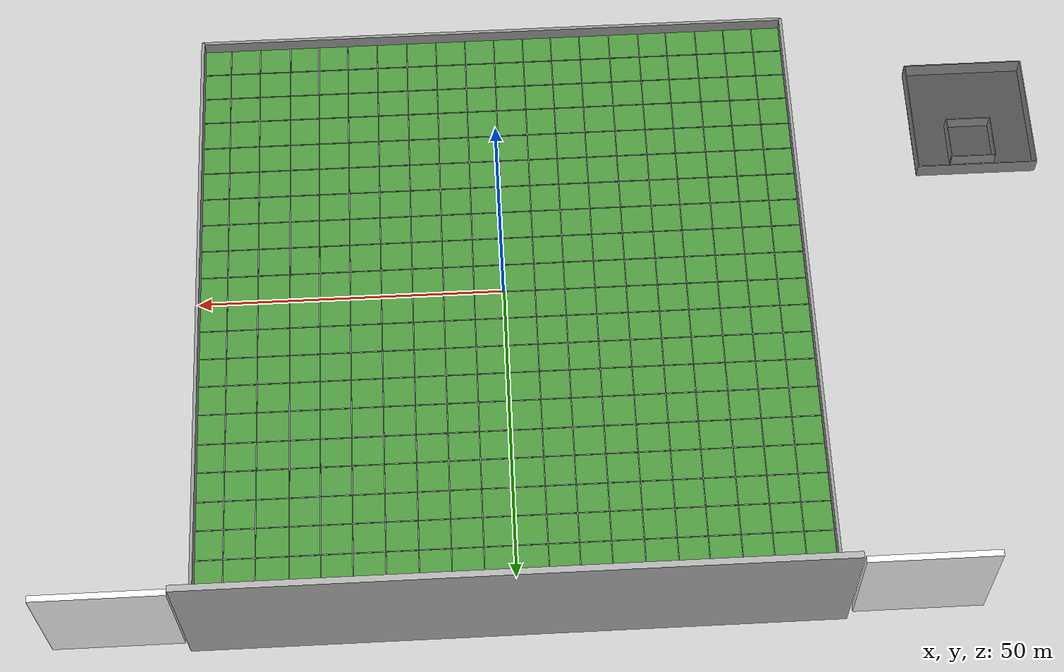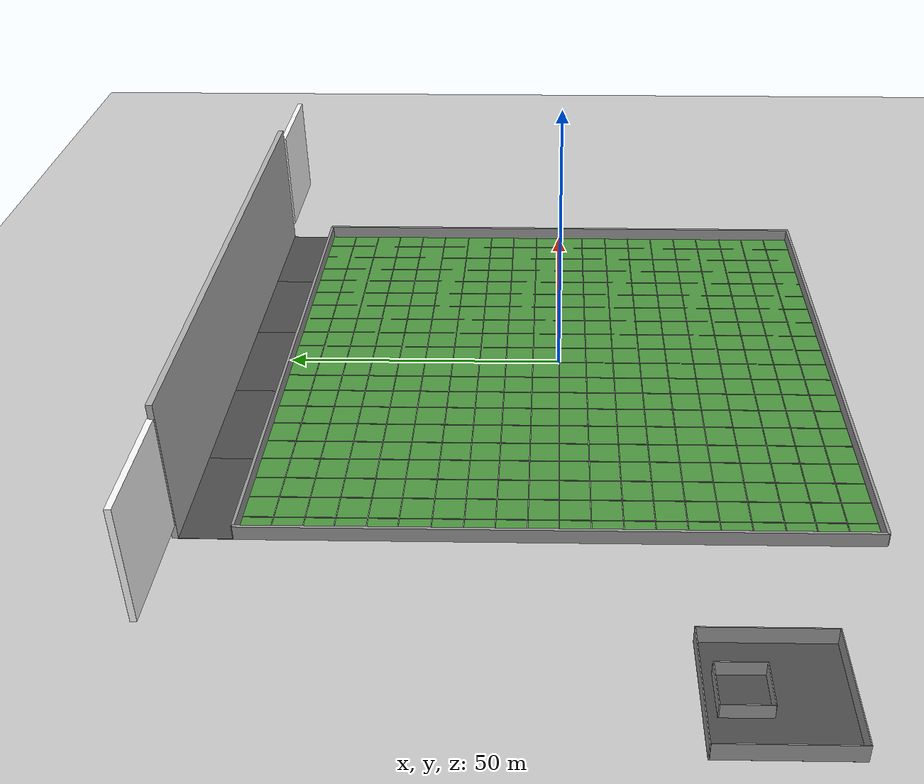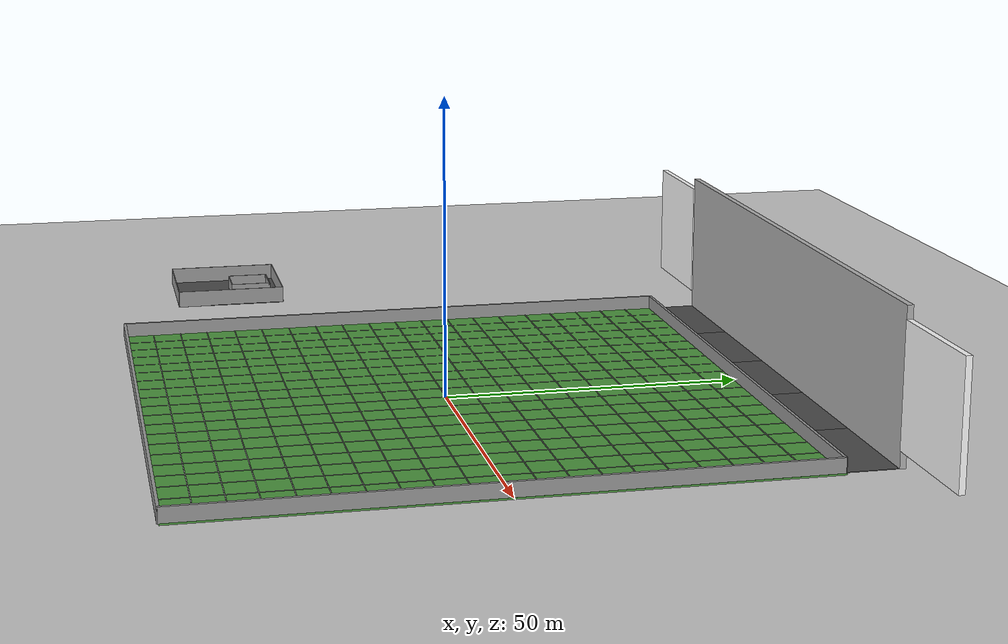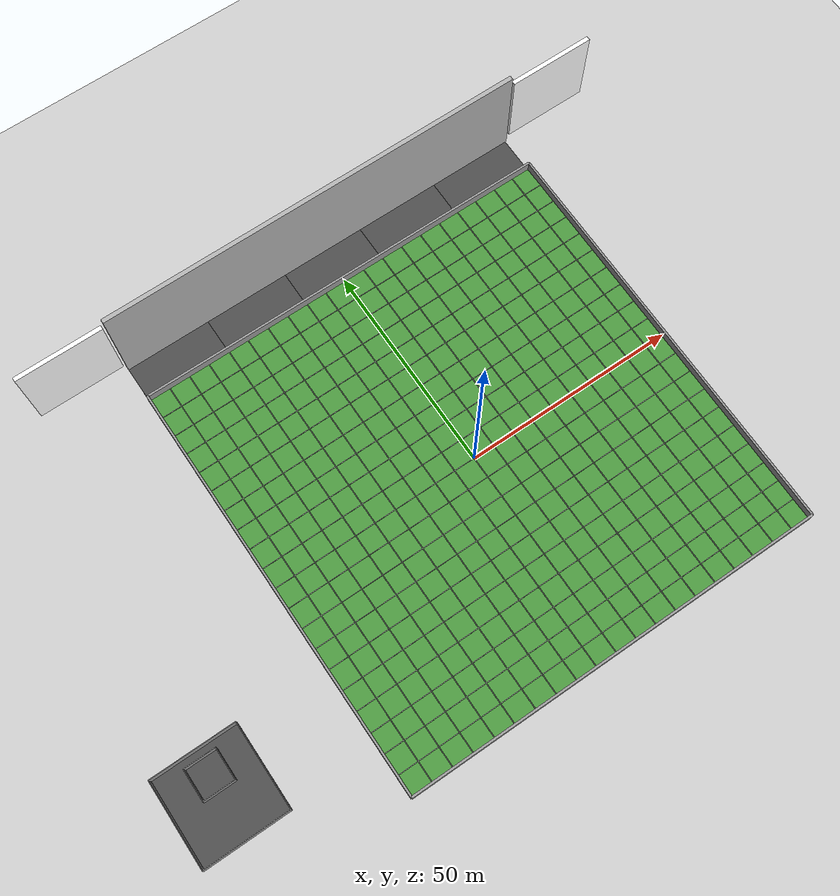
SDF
<sdf version="1.7">
 <world name="default">
  <light name="sun" type="directional">
   <pose>0 0 10 0 -0 0</pose>
   <diffuse>0.8 0.8 0.8 1</diffuse>
   <specular>0.2 0.2 0.2 1</specular>
   <attenuation>
    <range>1000</range>
    <constant>0.9</constant>
    <linear>0.01</linear>
    <quadratic>0.001</quadratic>
   </attenuation>
   <direction>-0.5 0.1 -0.9</direction>
   <spot><inner_angle>0</inner_angle><outer_angle>0</outer_angle><falloff>0</falloff></spot>
  </light>
  <model name="ground_plane">
   <static>1</static>
   <link name="link">
    <collision name="collision">
     <geometry><plane><normal>0 0 1</normal><size>100 100</size></plane></geometry>
     <surface><friction><ode><mu>100</mu><mu2>50</mu2></ode></friction></surface>
    </collision>
    <visual name="visual">
     <cast_shadows>0</cast_shadows>
     <geometry><plane><normal>0 0 1</normal><size>100 100</size></plane></geometry>
     <material>
      <script><uri>file://media/materials/scripts/gazebo.material</uri><name>Gazebo/Grey</name></script>
     </material>
    </visual>
   </link>
  </model>
  <gravity>0 0 -9.8</gravity>
  <magnetic_field>6e-06 2.3e-05 -4.2e-05</magnetic_field>
  <atmosphere type="adiabatic"/>
  <physics type="ode">
   <max_step_size>0.001</max_step_size>
   <real_time_factor>1</real_time_factor>
   <real_time_update_rate>1000</real_time_update_rate>
  </physics>
  <scene><ambient>0.4 0.4 0.4 1</ambient><background>0.7 0.7 0.7 1</background><shadows>1</shadows></scene>
  <spherical_coordinates>
   <surface_model>EARTH_WGS84</surface_model>
   <latitude_deg>0</latitude_deg>
   <longitude_deg>0</longitude_deg>
   <elevation>0</elevation>
   <heading_deg>0</heading_deg>
  </spherical_coordinates>
  <model name="gridline100m">
   <pose>0.007876 -6.97538 0 0 -0 0</pose>
   <link name="Wall_2">
    <collision name="Wall_2_Collision">
     <geometry><box><size>100 0.15 0.15</size></box></geometry>
     <pose>0 0 0.075 0 -0 0</pose>
    </collision>
    <visual name="Wall_2_Visual">
     <pose>0 0 0.075 0 -0 0</pose>
     <geometry><box><size>100 0.15 0.15</size></box></geometry>
     <material>
      <script><uri>file://media/materials/scripts/gazebo.material</uri><name>Gazebo/Grey</name></script>
      <ambient>0 0 0 1</ambient>
     </material>
     <meta><layer>0</layer></meta>
    </visual>
    <pose>2e-06 -3.05812 0 0 -0 0</pose>
   </link>
   <static>1</static>
  </model>
  <model name="gridline100m_clone">
   <pose>0.013 3.08479 0 0 -0 0</pose>
   <link name="Wall_2">
    <collision name="Wall_2_Collision">
     <geometry><box><size>100 0.15 0.15</size></box></geometry>
     <pose>0 0 0.075 0 -0 0</pose>
    </collision>
    <visual name="Wall_2_Visual">
     <pose>0 0 0.075 0 -0 0</pose>
     <geometry><box><size>100 0.15 0.15</size></box></geometry>
     <material>
      <script><uri>file://media/materials/scripts/gazebo.material</uri><name>Gazebo/Grey</name></script>
      <ambient>0 0 0 1</ambient>
     </material>
     <meta><layer>0</layer></meta>
    </visual>
    <pose>2e-06 -3.05812 0 0 -0 0</pose>
   </link>
   <static>1</static>
  </model>
  <model name="gridline100m_clone_0">
   <pose>-0.011254 13.0129 0 0 -0 0</pose>
   <link name="Wall_2">
    <collision name="Wall_2_Collision">
     <geometry><box><size>100 0.15 0.15</size></box></geometry>
     <pose>0 0 0.075 0 -0 0</pose>
    </collision>
    <visual name="Wall_2_Visual">
     <pose>0 0 0.075 0 -0 0</pose>
     <geometry><box><size>100 0.15 0.15</size></box></geometry>
     <material>
      <script><uri>file://media/materials/scripts/gazebo.material</uri><name>Gazebo/Grey</name></script>
      <ambient>0 0 0 1</ambient>
     </material>
     <meta><layer>0</layer></meta>
    </visual>
    <pose>2e-06 -3.05812 0 0 -0 0</pose>
   </link>
   <static>1</static>
  </model>
  <model name="gridline100m_clone_0_clone">
   <link name="Wall_2">
    <pose>2e-06 -3.05812 0 0 -0 1.571</pose>
    <inertial>
     <mass>1</mass>
     <inertia><ixx>1</ixx><ixy>0</ixy><ixz>0</ixz><iyy>1</iyy><iyz>0</iyz><izz>1</izz></inertia>
    </inertial>
    <visual name="Wall_2_Visual">
     <pose>0 0 0.075 0 -0 0</pose>
     <geometry><box><size>100 0.15 0.15</size></box></geometry>
     <material>
      <script><uri>file://media/materials/scripts/gazebo.material</uri><name>Gazebo/Grey</name></script>
      <ambient>0 0 0 1</ambient>
      <shader type="pixel"><normal_map>__default__</normal_map></shader>
      <diffuse>0.7 0.7 0.7 1</diffuse>
      <specular>0.01 0.01 0.01 1</specular>
      <emissive>0 0 0 1</emissive>
     </material>
     <meta><layer>0</layer></meta>
     <cast_shadows>0</cast_shadows>
    </visual>
    <collision name="Wall_2_Collision">
     <pose>0 0 0.075 0 -0 0</pose>
     <geometry><box><size>100 0.15 0.15</size></box></geometry>
     <surface>
      <friction>
       <ode><mu>1</mu><mu2>1</mu2><fdir1>0 0 0</fdir1><slip1>0</slip1><slip2>0</slip2></ode>
       <torsional>
        <coefficient>1</coefficient>
        <patch_radius>0</patch_radius>
        <surface_radius>0</surface_radius>
        <use_patch_radius>1</use_patch_radius>
        <ode><slip>0</slip></ode>
       </torsional>
      </friction>
      <bounce><restitution_coefficient>0</restitution_coefficient><threshold>1e+06</threshold></bounce>
      <contact>
       <collide_without_contact>0</collide_without_contact>
       <collide_without_contact_bitmask>1</collide_without_contact_bitmask>
       <collide_bitmask>1</collide_bitmask>
       <ode>
        <soft_cfm>0</soft_cfm>
        <soft_erp>0.2</soft_erp>
        <kp>1e+13</kp>
        <kd>1</kd>
        <max_vel>0.01</max_vel>
        <min_depth>0</min_depth>
       </ode>
       <bullet>
        <split_impulse>1</split_impulse>
        <split_impulse_penetration_threshold>-0.01</split_impulse_penetration_threshold>
        <soft_cfm>0</soft_cfm>
        <soft_erp>0.2</soft_erp>
        <kp>1e+13</kp>
        <kd>1</kd>
       </bullet>
      </contact>
     </surface>
    </collision>
   </link>
   <static>1</static>
   <pose>9.93727 3.17557 0 0 -0 0</pose>
  </model>
  <model name="gridline100m_clone_0_clone_clone">
   <link name="Wall_2">
    <pose>2e-06 -3.05812 0 0 -0 1.571</pose>
    <inertial>
     <mass>1</mass>
     <inertia><ixx>1</ixx><ixy>0</ixy><ixz>0</ixz><iyy>1</iyy><iyz>0</iyz><izz>1</izz></inertia>
    </inertial>
    <visual name="Wall_2_Visual">
     <pose>0 0 0.075 0 -0 0</pose>
     <geometry><box><size>100 0.15 0.15</size></box></geometry>
     <material>
      <script><uri>file://media/materials/scripts/gazebo.material</uri><name>Gazebo/Grey</name></script>
      <ambient>0 0 0 1</ambient>
      <shader type="pixel"><normal_map>__default__</normal_map></shader>
      <diffuse>0.7 0.7 0.7 1</diffuse>
      <specular>0.01 0.01 0.01 1</specular>
      <emissive>0 0 0 1</emissive>
     </material>
     <meta><layer>0</layer></meta>
     <cast_shadows>0</cast_shadows>
    </visual>
    <collision name="Wall_2_Collision">
     <pose>0 0 0.075 0 -0 0</pose>
     <geometry><box><size>100 0.15 0.15</size></box></geometry>
     <surface>
      <friction>
       <ode><mu>1</mu><mu2>1</mu2><fdir1>0 0 0</fdir1><slip1>0</slip1><slip2>0</slip2></ode>
       <torsional>
        <coefficient>1</coefficient>
        <patch_radius>0</patch_radius>
        <surface_radius>0</surface_radius>
        <use_patch_radius>1</use_patch_radius>
        <ode><slip>0</slip></ode>
       </torsional>
      </friction>
      <bounce><restitution_coefficient>0</restitution_coefficient><threshold>1e+06</threshold></bounce>
      <contact>
       <collide_without_contact>0</collide_without_contact>
       <collide_without_contact_bitmask>1</collide_without_contact_bitmask>
       <collide_bitmask>1</collide_bitmask>
       <ode>
        <soft_cfm>0</soft_cfm>
        <soft_erp>0.2</soft_erp>
        <kp>1e+13</kp>
        <kd>1</kd>
        <max_vel>0.01</max_vel>
        <min_depth>0</min_depth>
       </ode>
       <bullet>
        <split_impulse>1</split_impulse>
        <split_impulse_penetration_threshold>-0.01</split_impulse_penetration_threshold>
        <soft_cfm>0</soft_cfm>
        <soft_erp>0.2</soft_erp>
        <kp>1e+13</kp>
        <kd>1</kd>
       </bullet>
      </contact>
     </surface>
    </collision>
   </link>
   <static>1</static>
   <pose>-0.105326 3.11667 0 0 -0 0</pose>
  </model>
  <model name="gridline100m_clone_0_clone_clone_0">
   <link name="Wall_2">
    <pose>2e-06 -3.05812 0 0 -0 1.571</pose>
    <inertial>
     <mass>1</mass>
     <inertia><ixx>1</ixx><ixy>0</ixy><ixz>0</ixz><iyy>1</iyy><iyz>0</iyz><izz>1</izz></inertia>
    </inertial>
    <visual name="Wall_2_Visual">
     <pose>0 0 0.075 0 -0 0</pose>
     <geometry><box><size>100 0.15 0.15</size></box></geometry>
     <material>
      <script><uri>file://media/materials/scripts/gazebo.material</uri><name>Gazebo/Grey</name></script>
      <ambient>0 0 0 1</ambient>
      <shader type="pixel"><normal_map>__default__</normal_map></shader>
      <diffuse>0.7 0.7 0.7 1</diffuse>
      <specular>0.01 0.01 0.01 1</specular>
      <emissive>0 0 0 1</emissive>
     </material>
     <meta><layer>0</layer></meta>
     <cast_shadows>0</cast_shadows>
    </visual>
    <collision name="Wall_2_Collision">
     <pose>0 0 0.075 0 -0 0</pose>
     <geometry><box><size>100 0.15 0.15</size></box></geometry>
     <surface>
      <friction>
       <ode><mu>1</mu><mu2>1</mu2><fdir1>0 0 0</fdir1><slip1>0</slip1><slip2>0</slip2></ode>
       <torsional>
        <coefficient>1</coefficient>
        <patch_radius>0</patch_radius>
        <surface_radius>0</surface_radius>
        <use_patch_radius>1</use_patch_radius>
        <ode><slip>0</slip></ode>
       </torsional>
      </friction>
      <bounce><restitution_coefficient>0</restitution_coefficient><threshold>1e+06</threshold></bounce>
      <contact>
       <collide_without_contact>0</collide_without_contact>
       <collide_without_contact_bitmask>1</collide_without_contact_bitmask>
       <collide_bitmask>1</collide_bitmask>
       <ode>
        <soft_cfm>0</soft_cfm>
        <soft_erp>0.2</soft_erp>
        <kp>1e+13</kp>
        <kd>1</kd>
        <max_vel>0.01</max_vel>
        <min_depth>0</min_depth>
       </ode>
       <bullet>
        <split_impulse>1</split_impulse>
        <split_impulse_penetration_threshold>-0.01</split_impulse_penetration_threshold>
        <soft_cfm>0</soft_cfm>
        <soft_erp>0.2</soft_erp>
        <kp>1e+13</kp>
        <kd>1</kd>
       </bullet>
      </contact>
     </surface>
    </collision>
   </link>
   <static>1</static>
   <pose>-9.96377 3.09569 0 0 -0 0</pose>
  </model>
  <model name="gridline100m_clone_0_clone_clone_1">
   <link name="Wall_2">
    <pose>2e-06 -3.05812 0 0 -0 1.571</pose>
    <inertial>
     <mass>1</mass>
     <inertia><ixx>1</ixx><ixy>0</ixy><ixz>0</ixz><iyy>1</iyy><iyz>0</iyz><izz>1</izz></inertia>
    </inertial>
    <visual name="Wall_2_Visual">
     <pose>0 0 0.075 0 -0 0</pose>
     <geometry><box><size>100 0.15 0.15</size></box></geometry>
     <material>
      <script><uri>file://media/materials/scripts/gazebo.material</uri><name>Gazebo/Grey</name></script>
      <ambient>0 0 0 1</ambient>
      <shader type="pixel"><normal_map>__default__</normal_map></shader>
      <diffuse>0.7 0.7 0.7 1</diffuse>
      <specular>0.01 0.01 0.01 1</specular>
      <emissive>0 0 0 1</emissive>
     </material>
     <meta><layer>0</layer></meta>
     <cast_shadows>0</cast_shadows>
    </visual>
    <collision name="Wall_2_Collision">
     <pose>0 0 0.075 0 -0 0</pose>
     <geometry><box><size>100 0.15 0.15</size></box></geometry>
     <surface>
      <friction>
       <ode><mu>1</mu><mu2>1</mu2><fdir1>0 0 0</fdir1><slip1>0</slip1><slip2>0</slip2></ode>
       <torsional>
        <coefficient>1</coefficient>
        <patch_radius>0</patch_radius>
        <surface_radius>0</surface_radius>
        <use_patch_radius>1</use_patch_radius>
        <ode><slip>0</slip></ode>
       </torsional>
      </friction>
      <bounce><restitution_coefficient>0</restitution_coefficient><threshold>1e+06</threshold></bounce>
      <contact>
       <collide_without_contact>0</collide_without_contact>
       <collide_without_contact_bitmask>1</collide_without_contact_bitmask>
       <collide_bitmask>1</collide_bitmask>
       <ode>
        <soft_cfm>0</soft_cfm>
        <soft_erp>0.2</soft_erp>
        <kp>1e+13</kp>
        <kd>1</kd>
        <max_vel>0.01</max_vel>
        <min_depth>0</min_depth>
       </ode>
       <bullet>
        <split_impulse>1</split_impulse>
        <split_impulse_penetration_threshold>-0.01</split_impulse_penetration_threshold>
        <soft_cfm>0</soft_cfm>
        <soft_erp>0.2</soft_erp>
        <kp>1e+13</kp>
        <kd>1</kd>
       </bullet>
      </contact>
     </surface>
    </collision>
   </link>
   <static>1</static>
   <pose>20.1147 3.10463 0 0 -0 0</pose>
  </model>
  <model name="gridline100m_clone_0_clone_clone_1_clone">
   <link name="Wall_2">
    <pose>2e-06 -3.05812 0 0 -0 1.571</pose>
    <inertial>
     <mass>1</mass>
     <inertia><ixx>1</ixx><ixy>0</ixy><ixz>0</ixz><iyy>1</iyy><iyz>0</iyz><izz>1</izz></inertia>
    </inertial>
    <visual name="Wall_2_Visual">
     <pose>0 0 0.075 0 -0 0</pose>
     <geometry><box><size>100 0.15 0.15</size></box></geometry>
     <material>
      <script><uri>file://media/materials/scripts/gazebo.material</uri><name>Gazebo/Grey</name></script>
      <ambient>0 0 0 1</ambient>
      <shader type="pixel"><normal_map>__default__</normal_map></shader>
      <diffuse>0.7 0.7 0.7 1</diffuse>
      <specular>0.01 0.01 0.01 1</specular>
      <emissive>0 0 0 1</emissive>
     </material>
     <meta><layer>0</layer></meta>
     <cast_shadows>0</cast_shadows>
    </visual>
    <collision name="Wall_2_Collision">
     <pose>0 0 0.075 0 -0 0</pose>
     <geometry><box><size>100 0.15 0.15</size></box></geometry>
     <surface>
      <friction>
       <ode><mu>1</mu><mu2>1</mu2><fdir1>0 0 0</fdir1><slip1>0</slip1><slip2>0</slip2></ode>
       <torsional>
        <coefficient>1</coefficient>
        <patch_radius>0</patch_radius>
        <surface_radius>0</surface_radius>
        <use_patch_radius>1</use_patch_radius>
        <ode><slip>0</slip></ode>
       </torsional>
      </friction>
      <bounce><restitution_coefficient>0</restitution_coefficient><threshold>1e+06</threshold></bounce>
      <contact>
       <collide_without_contact>0</collide_without_contact>
       <collide_without_contact_bitmask>1</collide_without_contact_bitmask>
       <collide_bitmask>1</collide_bitmask>
       <ode>
        <soft_cfm>0</soft_cfm>
        <soft_erp>0.2</soft_erp>
        <kp>1e+13</kp>
        <kd>1</kd>
        <max_vel>0.01</max_vel>
        <min_depth>0</min_depth>
       </ode>
       <bullet>
        <split_impulse>1</split_impulse>
        <split_impulse_penetration_threshold>-0.01</split_impulse_penetration_threshold>
        <soft_cfm>0</soft_cfm>
        <soft_erp>0.2</soft_erp>
        <kp>1e+13</kp>
        <kd>1</kd>
       </bullet>
      </contact>
     </surface>
    </collision>
   </link>
   <static>1</static>
   <pose>30.2145 3.13489 0 0 -0 0</pose>
  </model>
  <model name="gridline100m_clone_0_clone_clone_1_clone_clone">
   <link name="Wall_2">
    <pose>2e-06 -3.05812 0 0 -0 1.571</pose>
    <inertial>
     <mass>1</mass>
     <inertia><ixx>1</ixx><ixy>0</ixy><ixz>0</ixz><iyy>1</iyy><iyz>0</iyz><izz>1</izz></inertia>
    </inertial>
    <visual name="Wall_2_Visual">
     <pose>0 0 0.075 0 -0 0</pose>
     <geometry><box><size>100 0.15 0.15</size></box></geometry>
     <material>
      <script><uri>file://media/materials/scripts/gazebo.material</uri><name>Gazebo/Grey</name></script>
      <ambient>0 0 0 1</ambient>
      <shader type="pixel"><normal_map>__default__</normal_map></shader>
      <diffuse>0.7 0.7 0.7 1</diffuse>
      <specular>0.01 0.01 0.01 1</specular>
      <emissive>0 0 0 1</emissive>
     </material>
     <meta><layer>0</layer></meta>
     <cast_shadows>0</cast_shadows>
    </visual>
    <collision name="Wall_2_Collision">
     <pose>0 0 0.075 0 -0 0</pose>
     <geometry><box><size>100 0.15 0.15</size></box></geometry>
     <surface>
      <friction>
       <ode><mu>1</mu><mu2>1</mu2><fdir1>0 0 0</fdir1><slip1>0</slip1><slip2>0</slip2></ode>
       <torsional>
        <coefficient>1</coefficient>
        <patch_radius>0</patch_radius>
        <surface_radius>0</surface_radius>
        <use_patch_radius>1</use_patch_radius>
        <ode><slip>0</slip></ode>
       </torsional>
      </friction>
      <bounce><restitution_coefficient>0</restitution_coefficient><threshold>1e+06</threshold></bounce>
      <contact>
       <collide_without_contact>0</collide_without_contact>
       <collide_without_contact_bitmask>1</collide_without_contact_bitmask>
       <collide_bitmask>1</collide_bitmask>
       <ode>
        <soft_cfm>0</soft_cfm>
        <soft_erp>0.2</soft_erp>
        <kp>1e+13</kp>
        <kd>1</kd>
        <max_vel>0.01</max_vel>
        <min_depth>0</min_depth>
       </ode>
       <bullet>
        <split_impulse>1</split_impulse>
        <split_impulse_penetration_threshold>-0.01</split_impulse_penetration_threshold>
        <soft_cfm>0</soft_cfm>
        <soft_erp>0.2</soft_erp>
        <kp>1e+13</kp>
        <kd>1</kd>
       </bullet>
      </contact>
     </surface>
    </collision>
   </link>
   <static>1</static>
   <pose>40.3256 3.07649 0 0 -0 0</pose>
  </model>
  <model name="gridline100m_clone_0_clone_clone_0_clone">
   <link name="Wall_2">
    <pose>2e-06 -3.05812 0 0 -0 1.571</pose>
    <inertial>
     <mass>1</mass>
     <inertia><ixx>1</ixx><ixy>0</ixy><ixz>0</ixz><iyy>1</iyy><iyz>0</iyz><izz>1</izz></inertia>
    </inertial>
    <visual name="Wall_2_Visual">
     <pose>0 0 0.075 0 -0 0</pose>
     <geometry><box><size>100 0.15 0.15</size></box></geometry>
     <material>
      <script><uri>file://media/materials/scripts/gazebo.material</uri><name>Gazebo/Grey</name></script>
      <ambient>0 0 0 1</ambient>
      <shader type="pixel"><normal_map>__default__</normal_map></shader>
      <diffuse>0.7 0.7 0.7 1</diffuse>
      <specular>0.01 0.01 0.01 1</specular>
      <emissive>0 0 0 1</emissive>
     </material>
     <meta><layer>0</layer></meta>
     <cast_shadows>0</cast_shadows>
    </visual>
    <collision name="Wall_2_Collision">
     <pose>0 0 0.075 0 -0 0</pose>
     <geometry><box><size>100 0.15 0.15</size></box></geometry>
     <surface>
      <friction>
       <ode><mu>1</mu><mu2>1</mu2><fdir1>0 0 0</fdir1><slip1>0</slip1><slip2>0</slip2></ode>
       <torsional>
        <coefficient>1</coefficient>
        <patch_radius>0</patch_radius>
        <surface_radius>0</surface_radius>
        <use_patch_radius>1</use_patch_radius>
        <ode><slip>0</slip></ode>
       </torsional>
      </friction>
      <bounce><restitution_coefficient>0</restitution_coefficient><threshold>1e+06</threshold></bounce>
      <contact>
       <collide_without_contact>0</collide_without_contact>
       <collide_without_contact_bitmask>1</collide_without_contact_bitmask>
       <collide_bitmask>1</collide_bitmask>
       <ode>
        <soft_cfm>0</soft_cfm>
        <soft_erp>0.2</soft_erp>
        <kp>1e+13</kp>
        <kd>1</kd>
        <max_vel>0.01</max_vel>
        <min_depth>0</min_depth>
       </ode>
       <bullet>
        <split_impulse>1</split_impulse>
        <split_impulse_penetration_threshold>-0.01</split_impulse_penetration_threshold>
        <soft_cfm>0</soft_cfm>
        <soft_erp>0.2</soft_erp>
        <kp>1e+13</kp>
        <kd>1</kd>
       </bullet>
      </contact>
     </surface>
    </collision>
   </link>
   <static>1</static>
   <pose>-20.0665 3.08574 0 0 -0 0</pose>
  </model>
  <model name="gridline100m_clone_0_clone_clone_0_clone_clone">
   <link name="Wall_2">
    <pose>2e-06 -3.05812 0 0 -0 1.571</pose>
    <inertial>
     <mass>1</mass>
     <inertia><ixx>1</ixx><ixy>0</ixy><ixz>0</ixz><iyy>1</iyy><iyz>0</iyz><izz>1</izz></inertia>
    </inertial>
    <visual name="Wall_2_Visual">
     <pose>0 0 0.075 0 -0 0</pose>
     <geometry><box><size>100 0.15 0.15</size></box></geometry>
     <material>
      <script><uri>file://media/materials/scripts/gazebo.material</uri><name>Gazebo/Grey</name></script>
      <ambient>0 0 0 1</ambient>
      <shader type="pixel"><normal_map>__default__</normal_map></shader>
      <diffuse>0.7 0.7 0.7 1</diffuse>
      <specular>0.01 0.01 0.01 1</specular>
      <emissive>0 0 0 1</emissive>
     </material>
     <meta><layer>0</layer></meta>
     <cast_shadows>0</cast_shadows>
    </visual>
    <collision name="Wall_2_Collision">
     <pose>0 0 0.075 0 -0 0</pose>
     <geometry><box><size>100 0.15 0.15</size></box></geometry>
     <surface>
      <friction>
       <ode><mu>1</mu><mu2>1</mu2><fdir1>0 0 0</fdir1><slip1>0</slip1><slip2>0</slip2></ode>
       <torsional>
        <coefficient>1</coefficient>
        <patch_radius>0</patch_radius>
        <surface_radius>0</surface_radius>
        <use_patch_radius>1</use_patch_radius>
        <ode><slip>0</slip></ode>
       </torsional>
      </friction>
      <bounce><restitution_coefficient>0</restitution_coefficient><threshold>1e+06</threshold></bounce>
      <contact>
       <collide_without_contact>0</collide_without_contact>
       <collide_without_contact_bitmask>1</collide_without_contact_bitmask>
       <collide_bitmask>1</collide_bitmask>
       <ode>
        <soft_cfm>0</soft_cfm>
        <soft_erp>0.2</soft_erp>
        <kp>1e+13</kp>
        <kd>1</kd>
        <max_vel>0.01</max_vel>
        <min_depth>0</min_depth>
       </ode>
       <bullet>
        <split_impulse>1</split_impulse>
        <split_impulse_penetration_threshold>-0.01</split_impulse_penetration_threshold>
        <soft_cfm>0</soft_cfm>
        <soft_erp>0.2</soft_erp>
        <kp>1e+13</kp>
        <kd>1</kd>
       </bullet>
      </contact>
     </surface>
    </collision>
   </link>
   <static>1</static>
   <pose>-30.0159 3.12682 0 0 -0 0</pose>
  </model>
  <model name="gridline100m_clone_0_clone_clone_0_clone_clone_clone">
   <link name="Wall_2">
    <pose>2e-06 -3.05812 0 0 -0 1.571</pose>
    <inertial>
     <mass>1</mass>
     <inertia><ixx>1</ixx><ixy>0</ixy><ixz>0</ixz><iyy>1</iyy><iyz>0</iyz><izz>1</izz></inertia>
    </inertial>
    <visual name="Wall_2_Visual">
     <pose>0 0 0.075 0 -0 0</pose>
     <geometry><box><size>100 0.15 0.15</size></box></geometry>
     <material>
      <script><uri>file://media/materials/scripts/gazebo.material</uri><name>Gazebo/Grey</name></script>
      <ambient>0 0 0 1</ambient>
      <shader type="pixel"><normal_map>__default__</normal_map></shader>
      <diffuse>0.7 0.7 0.7 1</diffuse>
      <specular>0.01 0.01 0.01 1</specular>
      <emissive>0 0 0 1</emissive>
     </material>
     <meta><layer>0</layer></meta>
     <cast_shadows>0</cast_shadows>
    </visual>
    <collision name="Wall_2_Collision">
     <pose>0 0 0.075 0 -0 0</pose>
     <geometry><box><size>100 0.15 0.15</size></box></geometry>
     <surface>
      <friction>
       <ode><mu>1</mu><mu2>1</mu2><fdir1>0 0 0</fdir1><slip1>0</slip1><slip2>0</slip2></ode>
       <torsional>
        <coefficient>1</coefficient>
        <patch_radius>0</patch_radius>
        <surface_radius>0</surface_radius>
        <use_patch_radius>1</use_patch_radius>
        <ode><slip>0</slip></ode>
       </torsional>
      </friction>
      <bounce><restitution_coefficient>0</restitution_coefficient><threshold>1e+06</threshold></bounce>
      <contact>
       <collide_without_contact>0</collide_without_contact>
       <collide_without_contact_bitmask>1</collide_without_contact_bitmask>
       <collide_bitmask>1</collide_bitmask>
       <ode>
        <soft_cfm>0</soft_cfm>
        <soft_erp>0.2</soft_erp>
        <kp>1e+13</kp>
        <kd>1</kd>
        <max_vel>0.01</max_vel>
        <min_depth>0</min_depth>
       </ode>
       <bullet>
        <split_impulse>1</split_impulse>
        <split_impulse_penetration_threshold>-0.01</split_impulse_penetration_threshold>
        <soft_cfm>0</soft_cfm>
        <soft_erp>0.2</soft_erp>
        <kp>1e+13</kp>
        <kd>1</kd>
       </bullet>
      </contact>
     </surface>
    </collision>
   </link>
   <static>1</static>
   <pose>-40.0496 3.09833 0 0 -0 0</pose>
  </model>
  <model name="gridline100m_clone_1">
   <pose>-0.046986 -16.9532 0 0 -0 0</pose>
   <link name="Wall_2">
    <collision name="Wall_2_Collision">
     <geometry><box><size>100 0.15 0.15</size></box></geometry>
     <pose>0 0 0.075 0 -0 0</pose>
    </collision>
    <visual name="Wall_2_Visual">
     <pose>0 0 0.075 0 -0 0</pose>
     <geometry><box><size>100 0.15 0.15</size></box></geometry>
     <material>
      <script><uri>file://media/materials/scripts/gazebo.material</uri><name>Gazebo/Grey</name></script>
      <ambient>0 0 0 1</ambient>
     </material>
     <meta><layer>0</layer></meta>
    </visual>
    <pose>2e-06 -3.05812 0 0 -0 0</pose>
   </link>
   <static>1</static>
  </model>
  <model name="gridline100m_clone_1_clone">
   <pose>0.0391 -26.9723 0 0 -0 0</pose>
   <link name="Wall_2">
    <collision name="Wall_2_Collision">
     <geometry><box><size>100 0.15 0.15</size></box></geometry>
     <pose>0 0 0.075 0 -0 0</pose>
    </collision>
    <visual name="Wall_2_Visual">
     <pose>0 0 0.075 0 -0 0</pose>
     <geometry><box><size>100 0.15 0.15</size></box></geometry>
     <material>
      <script><uri>file://media/materials/scripts/gazebo.material</uri><name>Gazebo/Grey</name></script>
      <ambient>0 0 0 1</ambient>
     </material>
     <meta><layer>0</layer></meta>
    </visual>
    <pose>2e-06 -3.05812 0 0 -0 0</pose>
   </link>
   <static>1</static>
  </model>
  <model name="gridline100m_clone_1_clone_clone">
   <pose>-0.033098 -36.9108 0 0 -0 0</pose>
   <link name="Wall_2">
    <collision name="Wall_2_Collision">
     <geometry><box><size>100 0.15 0.15</size></box></geometry>
     <pose>0 0 0.075 0 -0 0</pose>
    </collision>
    <visual name="Wall_2_Visual">
     <pose>0 0 0.075 0 -0 0</pose>
     <geometry><box><size>100 0.15 0.15</size></box></geometry>
     <material>
      <script><uri>file://media/materials/scripts/gazebo.material</uri><name>Gazebo/Grey</name></script>
      <ambient>0 0 0 1</ambient>
     </material>
     <meta><layer>0</layer></meta>
    </visual>
    <pose>2e-06 -3.05812 0 0 -0 0</pose>
   </link>
   <static>1</static>
  </model>
  <model name="gridline100m_clone_0_clone_0">
   <pose>-0.012985 22.9729 0 0 -0 0</pose>
   <link name="Wall_2">
    <collision name="Wall_2_Collision">
     <geometry><box><size>100 0.15 0.15</size></box></geometry>
     <pose>0 0 0.075 0 -0 0</pose>
    </collision>
    <visual name="Wall_2_Visual">
     <pose>0 0 0.075 0 -0 0</pose>
     <geometry><box><size>100 0.15 0.15</size></box></geometry>
     <material>
      <script><uri>file://media/materials/scripts/gazebo.material</uri><name>Gazebo/Grey</name></script>
      <ambient>0 0 0 1</ambient>
     </material>
     <meta><layer>0</layer></meta>
    </visual>
    <pose>2e-06 -3.05812 0 0 -0 0</pose>
   </link>
   <static>1</static>
  </model>
  <model name="gridline100m_clone_0_clone_0_clone">
   <pose>-0.008378 33.0432 0 0 -0 0</pose>
   <link name="Wall_2">
    <collision name="Wall_2_Collision">
     <geometry><box><size>100 0.15 0.15</size></box></geometry>
     <pose>0 0 0.075 0 -0 0</pose>
    </collision>
    <visual name="Wall_2_Visual">
     <pose>0 0 0.075 0 -0 0</pose>
     <geometry><box><size>100 0.15 0.15</size></box></geometry>
     <material>
      <script><uri>file://media/materials/scripts/gazebo.material</uri><name>Gazebo/Grey</name></script>
      <ambient>0 0 0 1</ambient>
     </material>
     <meta><layer>0</layer></meta>
    </visual>
    <pose>2e-06 -3.05812 0 0 -0 0</pose>
   </link>
   <static>1</static>
  </model>
  <model name="gridline100m_clone_0_clone_0_clone_clone">
   <pose>-0.009803 42.9182 0 0 -0 0</pose>
   <link name="Wall_2">
    <collision name="Wall_2_Collision">
     <geometry><box><size>100 0.15 0.15</size></box></geometry>
     <pose>0 0 0.075 0 -0 0</pose>
    </collision>
    <visual name="Wall_2_Visual">
     <pose>0 0 0.075 0 -0 0</pose>
     <geometry><box><size>100 0.15 0.15</size></box></geometry>
     <material>
      <script><uri>file://media/materials/scripts/gazebo.material</uri><name>Gazebo/Grey</name></script>
      <ambient>0 0 0 1</ambient>
     </material>
     <meta><layer>0</layer></meta>
    </visual>
    <pose>2e-06 -3.05812 0 0 -0 0</pose>
   </link>
   <static>1</static>
  </model>
  <model name="100mfence_clone_clone_clone">
   <link name="Wall_0">
    <pose>-13.0161 -13.4589 0 0 -0 1.571</pose>
    <inertial>
     <mass>75000</mass>
     <inertia>
      <ixx>39203.1</ixx>
      <ixy>0</ixy>
      <ixz>0</ixz>
      <iyy>6.25391e+07</iyy>
      <iyz>0</iyz>
      <izz>6.25001e+07</izz>
     </inertia>
    </inertial>
    <visual name="Wall_0_Visual">
     <pose>0 0 1.25 0 -0 0</pose>
     <geometry><box><size>100 0.5 2.5</size></box></geometry>
     <material>
      <script><uri>file://media/materials/scripts/gazebo.material</uri><name>Gazebo/Grey</name></script>
      <ambient>0.5 0.5 0.5 1</ambient>
      <shader type="pixel"><normal_map>__default__</normal_map></shader>
      <diffuse>0.5 0.5 0.5 1</diffuse>
      <specular>0.5 0.5 0.5 1</specular>
      <emissive>0 0 0 1</emissive>
     </material>
     <meta><layer>0</layer></meta>
     <cast_shadows>0</cast_shadows>
    </visual>
    <collision name="Wall_0_Collision">
     <pose>0 0 1.25 0 -0 0</pose>
     <geometry><box><size>100 0.2 2.5</size></box></geometry>
     <surface>
      <friction>
       <ode><mu>1</mu><mu2>1</mu2><fdir1>0 0 0</fdir1><slip1>0</slip1><slip2>0</slip2></ode>
       <torsional>
        <coefficient>1</coefficient>
        <patch_radius>0</patch_radius>
        <surface_radius>0</surface_radius>
        <use_patch_radius>1</use_patch_radius>
        <ode><slip>0</slip></ode>
       </torsional>
      </friction>
      <bounce><restitution_coefficient>0</restitution_coefficient><threshold>1e+06</threshold></bounce>
      <contact>
       <collide_without_contact>0</collide_without_contact>
       <collide_without_contact_bitmask>1</collide_without_contact_bitmask>
       <collide_bitmask>1</collide_bitmask>
       <ode>
        <soft_cfm>0</soft_cfm>
        <soft_erp>0.2</soft_erp>
        <kp>1e+13</kp>
        <kd>1</kd>
        <max_vel>0.01</max_vel>
        <min_depth>0</min_depth>
       </ode>
       <bullet>
        <split_impulse>1</split_impulse>
        <split_impulse_penetration_threshold>-0.01</split_impulse_penetration_threshold>
        <soft_cfm>0</soft_cfm>
        <soft_erp>0.2</soft_erp>
        <kp>1e+13</kp>
        <kd>1</kd>
       </bullet>
      </contact>
     </surface>
    </collision>
   </link>
   <static>1</static>
   <pose>62.9584 13.4532 0 0 -0 0</pose>
  </model>
  <model name="100mfence">
   <link name="Wall_0">
    <pose>-2e-06 -1.2425 0 0 -0 0</pose>
    <inertial>
     <mass>1</mass>
     <inertia><ixx>1</ixx><ixy>0</ixy><ixz>0</ixz><iyy>1</iyy><iyz>0</iyz><izz>1</izz></inertia>
    </inertial>
    <visual name="Wall_0_Visual">
     <pose>0 0 1.25 0 -0 0</pose>
     <geometry><box><size>100 0.5 2.5</size></box></geometry>
     <material>
      <script><uri>file://media/materials/scripts/gazebo.material</uri><name>Gazebo/Grey</name></script>
      <ambient>0.5 0.5 0.5 1</ambient>
      <shader type="pixel"><normal_map>__default__</normal_map></shader>
      <diffuse>0.5 0.5 0.5 1</diffuse>
      <specular>0.5 0.5 0.5 1</specular>
      <emissive>0 0 0 1</emissive>
     </material>
     <meta><layer>0</layer></meta>
     <cast_shadows>0</cast_shadows>
    </visual>
    <collision name="Wall_0_Collision">
     <pose>0 0 1.25 0 -0 0</pose>
     <geometry><box><size>100 0.15 2.5</size></box></geometry>
     <surface>
      <friction>
       <ode><mu>1</mu><mu2>1</mu2><fdir1>0 0 0</fdir1><slip1>0</slip1><slip2>0</slip2></ode>
       <torsional>
        <coefficient>1</coefficient>
        <patch_radius>0</patch_radius>
        <surface_radius>0</surface_radius>
        <use_patch_radius>1</use_patch_radius>
        <ode><slip>0</slip></ode>
       </torsional>
      </friction>
      <bounce><restitution_coefficient>0</restitution_coefficient><threshold>1e+06</threshold></bounce>
      <contact>
       <collide_without_contact>0</collide_without_contact>
       <collide_without_contact_bitmask>1</collide_without_contact_bitmask>
       <collide_bitmask>1</collide_bitmask>
       <ode>
        <soft_cfm>0</soft_cfm>
        <soft_erp>0.2</soft_erp>
        <kp>1e+13</kp>
        <kd>1</kd>
        <max_vel>0.01</max_vel>
        <min_depth>0</min_depth>
       </ode>
       <bullet>
        <split_impulse>1</split_impulse>
        <split_impulse_penetration_threshold>-0.01</split_impulse_penetration_threshold>
        <soft_cfm>0</soft_cfm>
        <soft_erp>0.2</soft_erp>
        <kp>1e+13</kp>
        <kd>1</kd>
       </bullet>
      </contact>
     </surface>
    </collision>
   </link>
   <static>1</static>
   <pose>1.6e-05 -48.6826 0 0 -0 0</pose>
  </model>
  <model name="100mfence_clone_clone">
   <link name="Wall_0">
    <pose>-13.0161 -13.4589 0 0 -0 1.571</pose>
    <inertial>
     <mass>1</mass>
     <inertia><ixx>1</ixx><ixy>0</ixy><ixz>0</ixz><iyy>1</iyy><iyz>0</iyz><izz>1</izz></inertia>
    </inertial>
    <visual name="Wall_0_Visual">
     <pose>0 0 1.25 0 -0 0</pose>
     <geometry><box><size>100 0.5 2.5</size></box></geometry>
     <material>
      <script><uri>file://media/materials/scripts/gazebo.material</uri><name>Gazebo/Grey</name></script>
      <ambient>0.5 0.5 0.5 1</ambient>
      <shader type="pixel"><normal_map>__default__</normal_map></shader>
      <diffuse>0.5 0.5 0.5 1</diffuse>
      <specular>0.5 0.5 0.5 1</specular>
      <emissive>0 0 0 1</emissive>
     </material>
     <meta><layer>0</layer></meta>
     <cast_shadows>0</cast_shadows>
    </visual>
    <collision name="Wall_0_Collision">
     <pose>0 0 1.25 0 -0 0</pose>
     <geometry><box><size>100 0.15 2.5</size></box></geometry>
     <surface>
      <friction>
       <ode><mu>1</mu><mu2>1</mu2><fdir1>0 0 0</fdir1><slip1>0</slip1><slip2>0</slip2></ode>
       <torsional>
        <coefficient>1</coefficient>
        <patch_radius>0</patch_radius>
        <surface_radius>0</surface_radius>
        <use_patch_radius>1</use_patch_radius>
        <ode><slip>0</slip></ode>
       </torsional>
      </friction>
      <bounce><restitution_coefficient>0</restitution_coefficient><threshold>1e+06</threshold></bounce>
      <contact>
       <collide_without_contact>0</collide_without_contact>
       <collide_without_contact_bitmask>1</collide_without_contact_bitmask>
       <collide_bitmask>1</collide_bitmask>
       <ode>
        <soft_cfm>0</soft_cfm>
        <soft_erp>0.2</soft_erp>
        <kp>1e+13</kp>
        <kd>1</kd>
        <max_vel>0.01</max_vel>
        <min_depth>0</min_depth>
       </ode>
       <bullet>
        <split_impulse>1</split_impulse>
        <split_impulse_penetration_threshold>-0.01</split_impulse_penetration_threshold>
        <soft_cfm>0</soft_cfm>
        <soft_erp>0.2</soft_erp>
        <kp>1e+13</kp>
        <kd>1</kd>
       </bullet>
      </contact>
     </surface>
    </collision>
   </link>
   <static>1</static>
   <pose>-36.9334 13.4626 0 0 -0 0</pose>
  </model>
  <model name="100mfence_clone">
   <link name="Wall_0">
    <pose>-2e-06 -1.2425 0 0 -0 0</pose>
    <inertial>
     <mass>1</mass>
     <inertia><ixx>1</ixx><ixy>0</ixy><ixz>0</ixz><iyy>1</iyy><iyz>0</iyz><izz>1</izz></inertia>
    </inertial>
    <visual name="Wall_0_Visual">
     <pose>0 0 1.25 0 -0 0</pose>
     <geometry><box><size>100 0.5 2.5</size></box></geometry>
     <material>
      <script><uri>file://media/materials/scripts/gazebo.material</uri><name>Gazebo/Grey</name></script>
      <ambient>0.5 0.5 0.5 1</ambient>
      <shader type="pixel"><normal_map>__default__</normal_map></shader>
      <diffuse>0.5 0.5 0.5 1</diffuse>
      <specular>0.5 0.5 0.5 1</specular>
      <emissive>0 0 0 1</emissive>
     </material>
     <meta><layer>0</layer></meta>
     <cast_shadows>0</cast_shadows>
    </visual>
    <collision name="Wall_0_Collision">
     <pose>0 0 1.25 0 -0 0</pose>
     <geometry><box><size>100 0.15 2.5</size></box></geometry>
     <surface>
      <friction>
       <ode><mu>1</mu><mu2>1</mu2><fdir1>0 0 0</fdir1><slip1>0</slip1><slip2>0</slip2></ode>
       <torsional>
        <coefficient>1</coefficient>
        <patch_radius>0</patch_radius>
        <surface_radius>0</surface_radius>
        <use_patch_radius>1</use_patch_radius>
        <ode><slip>0</slip></ode>
       </torsional>
      </friction>
      <bounce><restitution_coefficient>0</restitution_coefficient><threshold>1e+06</threshold></bounce>
      <contact>
       <collide_without_contact>0</collide_without_contact>
       <collide_without_contact_bitmask>1</collide_without_contact_bitmask>
       <collide_bitmask>1</collide_bitmask>
       <ode>
        <soft_cfm>0</soft_cfm>
        <soft_erp>0.2</soft_erp>
        <kp>1e+13</kp>
        <kd>1</kd>
        <max_vel>0.01</max_vel>
        <min_depth>0</min_depth>
       </ode>
       <bullet>
        <split_impulse>1</split_impulse>
        <split_impulse_penetration_threshold>-0.01</split_impulse_penetration_threshold>
        <soft_cfm>0</soft_cfm>
        <soft_erp>0.2</soft_erp>
        <kp>1e+13</kp>
        <kd>1</kd>
       </bullet>
      </contact>
     </surface>
    </collision>
   </link>
   <static>1</static>
   <pose>0.000191 51.1672 0 0 -0 0</pose>
  </model>
  <model name="helipadboundary_0">
   <link name="Wall_10">
    <pose>-0.049274 -3.675 0 0 -0 0</pose>
    <inertial>
     <mass>1</mass>
     <inertia><ixx>1</ixx><ixy>0</ixy><ixz>0</ixz><iyy>1</iyy><iyz>0</iyz><izz>1</izz></inertia>
    </inertial>
    <visual name="Wall_10_Visual">
     <pose>0 0 1.25 0 -0 0</pose>
     <geometry><box><size>7.5 0.15 2.5</size></box></geometry>
     <material>
      <script><uri>file://media/materials/scripts/gazebo.material</uri><name>Gazebo/Grey</name></script>
      <ambient>0.5 0.5 0.5 1</ambient>
      <shader type="pixel"><normal_map>__default__</normal_map></shader>
      <diffuse>0.5 0.5 0.5 1</diffuse>
      <specular>0.5 0.5 0.5 1</specular>
      <emissive>0 0 0 1</emissive>
     </material>
     <meta><layer>0</layer></meta>
     <cast_shadows>0</cast_shadows>
    </visual>
    <collision name="Wall_10_Collision">
     <pose>0 0 1.25 0 -0 0</pose>
     <geometry><box><size>7.5 0.15 2.5</size></box></geometry>
     <surface>
      <friction>
       <ode><mu>1</mu><mu2>1</mu2><fdir1>0 0 0</fdir1><slip1>0</slip1><slip2>0</slip2></ode>
       <torsional>
        <coefficient>1</coefficient>
        <patch_radius>0</patch_radius>
        <surface_radius>0</surface_radius>
        <use_patch_radius>1</use_patch_radius>
        <ode><slip>0</slip></ode>
       </torsional>
      </friction>
      <bounce><restitution_coefficient>0</restitution_coefficient><threshold>1e+06</threshold></bounce>
      <contact>
       <collide_without_contact>0</collide_without_contact>
       <collide_without_contact_bitmask>1</collide_without_contact_bitmask>
       <collide_bitmask>1</collide_bitmask>
       <ode>
        <soft_cfm>0</soft_cfm>
        <soft_erp>0.2</soft_erp>
        <kp>1e+13</kp>
        <kd>1</kd>
        <max_vel>0.01</max_vel>
        <min_depth>0</min_depth>
       </ode>
       <bullet>
        <split_impulse>1</split_impulse>
        <split_impulse_penetration_threshold>-0.01</split_impulse_penetration_threshold>
        <soft_cfm>0</soft_cfm>
        <soft_erp>0.2</soft_erp>
        <kp>1e+13</kp>
        <kd>1</kd>
       </bullet>
      </contact>
     </surface>
    </collision>
   </link>
   <link name="Wall_12">
    <pose>3.62573 0 0 0 -0 1.5708</pose>
    <inertial>
     <mass>1</mass>
     <inertia><ixx>1</ixx><ixy>0</ixy><ixz>0</ixz><iyy>1</iyy><iyz>0</iyz><izz>1</izz></inertia>
    </inertial>
    <visual name="Wall_12_Visual">
     <pose>0 0 1.25 0 -0 0</pose>
     <geometry><box><size>7.5 0.15 2.5</size></box></geometry>
     <material>
      <script><uri>file://media/materials/scripts/gazebo.material</uri><name>Gazebo/Grey</name></script>
      <ambient>0.5 0.5 0.5 1</ambient>
      <shader type="pixel"><normal_map>__default__</normal_map></shader>
      <diffuse>0.5 0.5 0.5 1</diffuse>
      <specular>0.5 0.5 0.5 1</specular>
      <emissive>0 0 0 1</emissive>
     </material>
     <meta><layer>0</layer></meta>
     <cast_shadows>0</cast_shadows>
    </visual>
    <collision name="Wall_12_Collision">
     <pose>0 0 1.25 0 -0 0</pose>
     <geometry><box><size>7.5 0.15 2.5</size></box></geometry>
     <surface>
      <friction>
       <ode><mu>1</mu><mu2>1</mu2><fdir1>0 0 0</fdir1><slip1>0</slip1><slip2>0</slip2></ode>
       <torsional>
        <coefficient>1</coefficient>
        <patch_radius>0</patch_radius>
        <surface_radius>0</surface_radius>
        <use_patch_radius>1</use_patch_radius>
        <ode><slip>0</slip></ode>
       </torsional>
      </friction>
      <bounce><restitution_coefficient>0</restitution_coefficient><threshold>1e+06</threshold></bounce>
      <contact>
       <collide_without_contact>0</collide_without_contact>
       <collide_without_contact_bitmask>1</collide_without_contact_bitmask>
       <collide_bitmask>1</collide_bitmask>
       <ode>
        <soft_cfm>0</soft_cfm>
        <soft_erp>0.2</soft_erp>
        <kp>1e+13</kp>
        <kd>1</kd>
        <max_vel>0.01</max_vel>
        <min_depth>0</min_depth>
       </ode>
       <bullet>
        <split_impulse>1</split_impulse>
        <split_impulse_penetration_threshold>-0.01</split_impulse_penetration_threshold>
        <soft_cfm>0</soft_cfm>
        <soft_erp>0.2</soft_erp>
        <kp>1e+13</kp>
        <kd>1</kd>
       </bullet>
      </contact>
     </surface>
    </collision>
   </link>
   <link name="Wall_13">
    <pose>-0.049274 3.675 0 0 -0 3.14159</pose>
    <inertial>
     <mass>1</mass>
     <inertia><ixx>1</ixx><ixy>0</ixy><ixz>0</ixz><iyy>1</iyy><iyz>0</iyz><izz>1</izz></inertia>
    </inertial>
    <visual name="Wall_13_Visual">
     <pose>0 0 1.25 0 -0 0</pose>
     <geometry><box><size>7.5 0.15 2.5</size></box></geometry>
     <material>
      <script><uri>file://media/materials/scripts/gazebo.material</uri><name>Gazebo/Grey</name></script>
      <ambient>0.5 0.5 0.5 1</ambient>
      <shader type="pixel"><normal_map>__default__</normal_map></shader>
      <diffuse>0.5 0.5 0.5 1</diffuse>
      <specular>0.5 0.5 0.5 1</specular>
      <emissive>0 0 0 1</emissive>
     </material>
     <meta><layer>0</layer></meta>
     <cast_shadows>0</cast_shadows>
    </visual>
    <collision name="Wall_13_Collision">
     <pose>0 0 1.25 0 -0 0</pose>
     <geometry><box><size>7.5 0.15 2.5</size></box></geometry>
     <surface>
      <friction>
       <ode><mu>1</mu><mu2>1</mu2><fdir1>0 0 0</fdir1><slip1>0</slip1><slip2>0</slip2></ode>
       <torsional>
        <coefficient>1</coefficient>
        <patch_radius>0</patch_radius>
        <surface_radius>0</surface_radius>
        <use_patch_radius>1</use_patch_radius>
        <ode><slip>0</slip></ode>
       </torsional>
      </friction>
      <bounce><restitution_coefficient>0</restitution_coefficient><threshold>1e+06</threshold></bounce>
      <contact>
       <collide_without_contact>0</collide_without_contact>
       <collide_without_contact_bitmask>1</collide_without_contact_bitmask>
       <collide_bitmask>1</collide_bitmask>
       <ode>
        <soft_cfm>0</soft_cfm>
        <soft_erp>0.2</soft_erp>
        <kp>1e+13</kp>
        <kd>1</kd>
        <max_vel>0.01</max_vel>
        <min_depth>0</min_depth>
       </ode>
       <bullet>
        <split_impulse>1</split_impulse>
        <split_impulse_penetration_threshold>-0.01</split_impulse_penetration_threshold>
        <soft_cfm>0</soft_cfm>
        <soft_erp>0.2</soft_erp>
        <kp>1e+13</kp>
        <kd>1</kd>
       </bullet>
      </contact>
     </surface>
    </collision>
   </link>
   <link name="Wall_14">
    <pose>-3.72427 0 0 0 0 -1.5708</pose>
    <inertial>
     <mass>1</mass>
     <inertia><ixx>1</ixx><ixy>0</ixy><ixz>0</ixz><iyy>1</iyy><iyz>0</iyz><izz>1</izz></inertia>
    </inertial>
    <visual name="Wall_14_Visual">
     <pose>0 0 1.25 0 -0 0</pose>
     <geometry><box><size>7.5 0.15 2.5</size></box></geometry>
     <material>
      <script><uri>file://media/materials/scripts/gazebo.material</uri><name>Gazebo/Grey</name></script>
      <ambient>0.5 0.5 0.5 1</ambient>
      <shader type="pixel"><normal_map>__default__</normal_map></shader>
      <diffuse>0.5 0.5 0.5 1</diffuse>
      <specular>0.5 0.5 0.5 1</specular>
      <emissive>0 0 0 1</emissive>
     </material>
     <meta><layer>0</layer></meta>
     <cast_shadows>0</cast_shadows>
    </visual>
    <collision name="Wall_14_Collision">
     <pose>0 0 1.25 0 -0 0</pose>
     <geometry><box><size>7.5 0.15 2.5</size></box></geometry>
     <surface>
      <friction>
       <ode><mu>1</mu><mu2>1</mu2><fdir1>0 0 0</fdir1><slip1>0</slip1><slip2>0</slip2></ode>
       <torsional>
        <coefficient>1</coefficient>
        <patch_radius>0</patch_radius>
        <surface_radius>0</surface_radius>
        <use_patch_radius>1</use_patch_radius>
        <ode><slip>0</slip></ode>
       </torsional>
      </friction>
      <bounce><restitution_coefficient>0</restitution_coefficient><threshold>1e+06</threshold></bounce>
      <contact>
       <collide_without_contact>0</collide_without_contact>
       <collide_without_contact_bitmask>1</collide_without_contact_bitmask>
       <collide_bitmask>1</collide_bitmask>
       <ode>
        <soft_cfm>0</soft_cfm>
        <soft_erp>0.2</soft_erp>
        <kp>1e+13</kp>
        <kd>1</kd>
        <max_vel>0.01</max_vel>
        <min_depth>0</min_depth>
       </ode>
       <bullet>
        <split_impulse>1</split_impulse>
        <split_impulse_penetration_threshold>-0.01</split_impulse_penetration_threshold>
        <soft_cfm>0</soft_cfm>
        <soft_erp>0.2</soft_erp>
        <kp>1e+13</kp>
        <kd>1</kd>
       </bullet>
      </contact>
     </surface>
    </collision>
   </link>
   <static>1</static>
   <pose>-79.8103 -24.2514 0 0 -0 0</pose>
  </model>
  <model name="gridline100m_clone_0_clone_clone_0_clone_clone_clone_clone">
   <link name="Wall_2">
    <pose>2e-06 -3.05812 0 0 -0 1.571</pose>
    <inertial>
     <mass>1</mass>
     <inertia><ixx>1</ixx><ixy>0</ixy><ixz>0</ixz><iyy>1</iyy><iyz>0</iyz><izz>1</izz></inertia>
    </inertial>
    <visual name="Wall_2_Visual">
     <pose>0 0 0.075 0 -0 0</pose>
     <geometry><box><size>100 0.15 0.15</size></box></geometry>
     <material>
      <script><uri>file://media/materials/scripts/gazebo.material</uri><name>Gazebo/Grey</name></script>
      <ambient>0 0 0 1</ambient>
      <shader type="pixel"><normal_map>__default__</normal_map></shader>
      <diffuse>0.7 0.7 0.7 1</diffuse>
      <specular>0.01 0.01 0.01 1</specular>
      <emissive>0 0 0 1</emissive>
     </material>
     <meta><layer>0</layer></meta>
     <cast_shadows>0</cast_shadows>
    </visual>
    <collision name="Wall_2_Collision">
     <pose>0 0 0.075 0 -0 0</pose>
     <geometry><box><size>100 0.15 0.15</size></box></geometry>
     <surface>
      <friction>
       <ode><mu>1</mu><mu2>1</mu2><fdir1>0 0 0</fdir1><slip1>0</slip1><slip2>0</slip2></ode>
       <torsional>
        <coefficient>1</coefficient>
        <patch_radius>0</patch_radius>
        <surface_radius>0</surface_radius>
        <use_patch_radius>1</use_patch_radius>
        <ode><slip>0</slip></ode>
       </torsional>
      </friction>
      <bounce><restitution_coefficient>0</restitution_coefficient><threshold>1e+06</threshold></bounce>
      <contact>
       <collide_without_contact>0</collide_without_contact>
       <collide_without_contact_bitmask>1</collide_without_contact_bitmask>
       <collide_bitmask>1</collide_bitmask>
       <ode>
        <soft_cfm>0</soft_cfm>
        <soft_erp>0.2</soft_erp>
        <kp>1e+13</kp>
        <kd>1</kd>
        <max_vel>0.01</max_vel>
        <min_depth>0</min_depth>
       </ode>
       <bullet>
        <split_impulse>1</split_impulse>
        <split_impulse_penetration_threshold>-0.01</split_impulse_penetration_threshold>
        <soft_cfm>0</soft_cfm>
        <soft_erp>0.2</soft_erp>
        <kp>1e+13</kp>
        <kd>1</kd>
       </bullet>
      </contact>
     </surface>
    </collision>
   </link>
   <static>1</static>
   <pose>-44.9764 2.88672 0 0 -0 0</pose>
  </model>
  <model name="gridline100m_clone_0_clone_clone_0_clone_clone_clone_clone_clone">
   <link name="Wall_2">
    <pose>2e-06 -3.05812 0 0 -0 1.571</pose>
    <inertial>
     <mass>1</mass>
     <inertia><ixx>1</ixx><ixy>0</ixy><ixz>0</ixz><iyy>1</iyy><iyz>0</iyz><izz>1</izz></inertia>
    </inertial>
    <visual name="Wall_2_Visual">
     <pose>0 0 0.075 0 -0 0</pose>
     <geometry><box><size>100 0.15 0.15</size></box></geometry>
     <material>
      <script><uri>file://media/materials/scripts/gazebo.material</uri><name>Gazebo/Grey</name></script>
      <ambient>0 0 0 1</ambient>
      <shader type="pixel"><normal_map>__default__</normal_map></shader>
      <diffuse>0.7 0.7 0.7 1</diffuse>
      <specular>0.01 0.01 0.01 1</specular>
      <emissive>0 0 0 1</emissive>
     </material>
     <meta><layer>0</layer></meta>
     <cast_shadows>0</cast_shadows>
    </visual>
    <collision name="Wall_2_Collision">
     <pose>0 0 0.075 0 -0 0</pose>
     <geometry><box><size>100 0.15 0.15</size></box></geometry>
     <surface>
      <friction>
       <ode><mu>1</mu><mu2>1</mu2><fdir1>0 0 0</fdir1><slip1>0</slip1><slip2>0</slip2></ode>
       <torsional>
        <coefficient>1</coefficient>
        <patch_radius>0</patch_radius>
        <surface_radius>0</surface_radius>
        <use_patch_radius>1</use_patch_radius>
        <ode><slip>0</slip></ode>
       </torsional>
      </friction>
      <bounce><restitution_coefficient>0</restitution_coefficient><threshold>1e+06</threshold></bounce>
      <contact>
       <collide_without_contact>0</collide_without_contact>
       <collide_without_contact_bitmask>1</collide_without_contact_bitmask>
       <collide_bitmask>1</collide_bitmask>
       <ode>
        <soft_cfm>0</soft_cfm>
        <soft_erp>0.2</soft_erp>
        <kp>1e+13</kp>
        <kd>1</kd>
        <max_vel>0.01</max_vel>
        <min_depth>0</min_depth>
       </ode>
       <bullet>
        <split_impulse>1</split_impulse>
        <split_impulse_penetration_threshold>-0.01</split_impulse_penetration_threshold>
        <soft_cfm>0</soft_cfm>
        <soft_erp>0.2</soft_erp>
        <kp>1e+13</kp>
        <kd>1</kd>
       </bullet>
      </contact>
     </surface>
    </collision>
   </link>
   <static>1</static>
   <pose>-35.1397 2.90502 0 0 -0 0</pose>
  </model>
  <model name="gridline100m_clone_0_clone_clone_0_clone_clone_clone_clone_clone_0">
   <link name="Wall_2">
    <pose>2e-06 -3.05812 0 0 -0 1.571</pose>
    <inertial>
     <mass>1</mass>
     <inertia><ixx>1</ixx><ixy>0</ixy><ixz>0</ixz><iyy>1</iyy><iyz>0</iyz><izz>1</izz></inertia>
    </inertial>
    <visual name="Wall_2_Visual">
     <pose>0 0 0.075 0 -0 0</pose>
     <geometry><box><size>100 0.15 0.15</size></box></geometry>
     <material>
      <script><uri>file://media/materials/scripts/gazebo.material</uri><name>Gazebo/Grey</name></script>
      <ambient>0 0 0 1</ambient>
      <shader type="pixel"><normal_map>__default__</normal_map></shader>
      <diffuse>0.7 0.7 0.7 1</diffuse>
      <specular>0.01 0.01 0.01 1</specular>
      <emissive>0 0 0 1</emissive>
     </material>
     <meta><layer>0</layer></meta>
     <cast_shadows>0</cast_shadows>
    </visual>
    <collision name="Wall_2_Collision">
     <pose>0 0 0.075 0 -0 0</pose>
     <geometry><box><size>100 0.15 0.15</size></box></geometry>
     <surface>
      <friction>
       <ode><mu>1</mu><mu2>1</mu2><fdir1>0 0 0</fdir1><slip1>0</slip1><slip2>0</slip2></ode>
       <torsional>
        <coefficient>1</coefficient>
        <patch_radius>0</patch_radius>
        <surface_radius>0</surface_radius>
        <use_patch_radius>1</use_patch_radius>
        <ode><slip>0</slip></ode>
       </torsional>
      </friction>
      <bounce><restitution_coefficient>0</restitution_coefficient><threshold>1e+06</threshold></bounce>
      <contact>
       <collide_without_contact>0</collide_without_contact>
       <collide_without_contact_bitmask>1</collide_without_contact_bitmask>
       <collide_bitmask>1</collide_bitmask>
       <ode>
        <soft_cfm>0</soft_cfm>
        <soft_erp>0.2</soft_erp>
        <kp>1e+13</kp>
        <kd>1</kd>
        <max_vel>0.01</max_vel>
        <min_depth>0</min_depth>
       </ode>
       <bullet>
        <split_impulse>1</split_impulse>
        <split_impulse_penetration_threshold>-0.01</split_impulse_penetration_threshold>
        <soft_cfm>0</soft_cfm>
        <soft_erp>0.2</soft_erp>
        <kp>1e+13</kp>
        <kd>1</kd>
       </bullet>
      </contact>
     </surface>
    </collision>
   </link>
   <static>1</static>
   <pose>-25.1946 3.11028 0 0 -0 0</pose>
  </model>
  <model name="gridline100m_clone_0_clone_clone_0_clone_clone_clone_clone_clone_1">
   <link name="Wall_2">
    <pose>2e-06 -3.05812 0 0 -0 1.571</pose>
    <inertial>
     <mass>1</mass>
     <inertia><ixx>1</ixx><ixy>0</ixy><ixz>0</ixz><iyy>1</iyy><iyz>0</iyz><izz>1</izz></inertia>
    </inertial>
    <visual name="Wall_2_Visual">
     <pose>0 0 0.075 0 -0 0</pose>
     <geometry><box><size>100 0.15 0.15</size></box></geometry>
     <material>
      <script><uri>file://media/materials/scripts/gazebo.material</uri><name>Gazebo/Grey</name></script>
      <ambient>0 0 0 1</ambient>
      <shader type="pixel"><normal_map>__default__</normal_map></shader>
      <diffuse>0.7 0.7 0.7 1</diffuse>
      <specular>0.01 0.01 0.01 1</specular>
      <emissive>0 0 0 1</emissive>
     </material>
     <meta><layer>0</layer></meta>
     <cast_shadows>0</cast_shadows>
    </visual>
    <collision name="Wall_2_Collision">
     <pose>0 0 0.075 0 -0 0</pose>
     <geometry><box><size>100 0.15 0.15</size></box></geometry>
     <surface>
      <friction>
       <ode><mu>1</mu><mu2>1</mu2><fdir1>0 0 0</fdir1><slip1>0</slip1><slip2>0</slip2></ode>
       <torsional>
        <coefficient>1</coefficient>
        <patch_radius>0</patch_radius>
        <surface_radius>0</surface_radius>
        <use_patch_radius>1</use_patch_radius>
        <ode><slip>0</slip></ode>
       </torsional>
      </friction>
      <bounce><restitution_coefficient>0</restitution_coefficient><threshold>1e+06</threshold></bounce>
      <contact>
       <collide_without_contact>0</collide_without_contact>
       <collide_without_contact_bitmask>1</collide_without_contact_bitmask>
       <collide_bitmask>1</collide_bitmask>
       <ode>
        <soft_cfm>0</soft_cfm>
        <soft_erp>0.2</soft_erp>
        <kp>1e+13</kp>
        <kd>1</kd>
        <max_vel>0.01</max_vel>
        <min_depth>0</min_depth>
       </ode>
       <bullet>
        <split_impulse>1</split_impulse>
        <split_impulse_penetration_threshold>-0.01</split_impulse_penetration_threshold>
        <soft_cfm>0</soft_cfm>
        <soft_erp>0.2</soft_erp>
        <kp>1e+13</kp>
        <kd>1</kd>
       </bullet>
      </contact>
     </surface>
    </collision>
   </link>
   <static>1</static>
   <pose>-14.9493 3.16662 0 0 -0 0</pose>
  </model>
  <model name="gridline100m_clone_0_clone_clone_0_clone_clone_clone_clone_clone_2">
   <link name="Wall_2">
    <pose>2e-06 -3.05812 0 0 -0 1.571</pose>
    <inertial>
     <mass>1</mass>
     <inertia><ixx>1</ixx><ixy>0</ixy><ixz>0</ixz><iyy>1</iyy><iyz>0</iyz><izz>1</izz></inertia>
    </inertial>
    <visual name="Wall_2_Visual">
     <pose>0 0 0.075 0 -0 0</pose>
     <geometry><box><size>100 0.15 0.15</size></box></geometry>
     <material>
      <script><uri>file://media/materials/scripts/gazebo.material</uri><name>Gazebo/Grey</name></script>
      <ambient>0 0 0 1</ambient>
      <shader type="pixel"><normal_map>__default__</normal_map></shader>
      <diffuse>0.7 0.7 0.7 1</diffuse>
      <specular>0.01 0.01 0.01 1</specular>
      <emissive>0 0 0 1</emissive>
     </material>
     <meta><layer>0</layer></meta>
     <cast_shadows>0</cast_shadows>
    </visual>
    <collision name="Wall_2_Collision">
     <pose>0 0 0.075 0 -0 0</pose>
     <geometry><box><size>100 0.15 0.15</size></box></geometry>
     <surface>
      <friction>
       <ode><mu>1</mu><mu2>1</mu2><fdir1>0 0 0</fdir1><slip1>0</slip1><slip2>0</slip2></ode>
       <torsional>
        <coefficient>1</coefficient>
        <patch_radius>0</patch_radius>
        <surface_radius>0</surface_radius>
        <use_patch_radius>1</use_patch_radius>
        <ode><slip>0</slip></ode>
       </torsional>
      </friction>
      <bounce><restitution_coefficient>0</restitution_coefficient><threshold>1e+06</threshold></bounce>
      <contact>
       <collide_without_contact>0</collide_without_contact>
       <collide_without_contact_bitmask>1</collide_without_contact_bitmask>
       <collide_bitmask>1</collide_bitmask>
       <ode>
        <soft_cfm>0</soft_cfm>
        <soft_erp>0.2</soft_erp>
        <kp>1e+13</kp>
        <kd>1</kd>
        <max_vel>0.01</max_vel>
        <min_depth>0</min_depth>
       </ode>
       <bullet>
        <split_impulse>1</split_impulse>
        <split_impulse_penetration_threshold>-0.01</split_impulse_penetration_threshold>
        <soft_cfm>0</soft_cfm>
        <soft_erp>0.2</soft_erp>
        <kp>1e+13</kp>
        <kd>1</kd>
       </bullet>
      </contact>
     </surface>
    </collision>
   </link>
   <static>1</static>
   <pose>-5.09112 3.1995 0 0 -0 0</pose>
  </model>
  <model name="gridline100m_clone_0_clone_clone_0_clone_clone_clone_clone_clone_3">
   <link name="Wall_2">
    <pose>2e-06 -3.05812 0 0 -0 1.571</pose>
    <inertial>
     <mass>1</mass>
     <inertia><ixx>1</ixx><ixy>0</ixy><ixz>0</ixz><iyy>1</iyy><iyz>0</iyz><izz>1</izz></inertia>
    </inertial>
    <visual name="Wall_2_Visual">
     <pose>0 0 0.075 0 -0 0</pose>
     <geometry><box><size>100 0.15 0.15</size></box></geometry>
     <material>
      <script><uri>file://media/materials/scripts/gazebo.material</uri><name>Gazebo/Grey</name></script>
      <ambient>0 0 0 1</ambient>
      <shader type="pixel"><normal_map>__default__</normal_map></shader>
      <diffuse>0.7 0.7 0.7 1</diffuse>
      <specular>0.01 0.01 0.01 1</specular>
      <emissive>0 0 0 1</emissive>
     </material>
     <meta><layer>0</layer></meta>
     <cast_shadows>0</cast_shadows>
    </visual>
    <collision name="Wall_2_Collision">
     <pose>0 0 0.075 0 -0 0</pose>
     <geometry><box><size>100 0.15 0.15</size></box></geometry>
     <surface>
      <friction>
       <ode><mu>1</mu><mu2>1</mu2><fdir1>0 0 0</fdir1><slip1>0</slip1><slip2>0</slip2></ode>
       <torsional>
        <coefficient>1</coefficient>
        <patch_radius>0</patch_radius>
        <surface_radius>0</surface_radius>
        <use_patch_radius>1</use_patch_radius>
        <ode><slip>0</slip></ode>
       </torsional>
      </friction>
      <bounce><restitution_coefficient>0</restitution_coefficient><threshold>1e+06</threshold></bounce>
      <contact>
       <collide_without_contact>0</collide_without_contact>
       <collide_without_contact_bitmask>1</collide_without_contact_bitmask>
       <collide_bitmask>1</collide_bitmask>
       <ode>
        <soft_cfm>0</soft_cfm>
        <soft_erp>0.2</soft_erp>
        <kp>1e+13</kp>
        <kd>1</kd>
        <max_vel>0.01</max_vel>
        <min_depth>0</min_depth>
       </ode>
       <bullet>
        <split_impulse>1</split_impulse>
        <split_impulse_penetration_threshold>-0.01</split_impulse_penetration_threshold>
        <soft_cfm>0</soft_cfm>
        <soft_erp>0.2</soft_erp>
        <kp>1e+13</kp>
        <kd>1</kd>
       </bullet>
      </contact>
     </surface>
    </collision>
   </link>
   <static>1</static>
   <pose>4.91478 3.18273 0 0 -0 0</pose>
  </model>
  <model name="gridline100m_clone_0_clone_clone_0_clone_clone_clone_clone_clone_4">
   <link name="Wall_2">
    <pose>2e-06 -3.05812 0 0 -0 1.571</pose>
    <inertial>
     <mass>1</mass>
     <inertia><ixx>1</ixx><ixy>0</ixy><ixz>0</ixz><iyy>1</iyy><iyz>0</iyz><izz>1</izz></inertia>
    </inertial>
    <visual name="Wall_2_Visual">
     <pose>0 0 0.075 0 -0 0</pose>
     <geometry><box><size>100 0.15 0.15</size></box></geometry>
     <material>
      <script><uri>file://media/materials/scripts/gazebo.material</uri><name>Gazebo/Grey</name></script>
      <ambient>0 0 0 1</ambient>
      <shader type="pixel"><normal_map>__default__</normal_map></shader>
      <diffuse>0.7 0.7 0.7 1</diffuse>
      <specular>0.01 0.01 0.01 1</specular>
      <emissive>0 0 0 1</emissive>
     </material>
     <meta><layer>0</layer></meta>
     <cast_shadows>0</cast_shadows>
    </visual>
    <collision name="Wall_2_Collision">
     <pose>0 0 0.075 0 -0 0</pose>
     <geometry><box><size>100 0.15 0.15</size></box></geometry>
     <surface>
      <friction>
       <ode><mu>1</mu><mu2>1</mu2><fdir1>0 0 0</fdir1><slip1>0</slip1><slip2>0</slip2></ode>
       <torsional>
        <coefficient>1</coefficient>
        <patch_radius>0</patch_radius>
        <surface_radius>0</surface_radius>
        <use_patch_radius>1</use_patch_radius>
        <ode><slip>0</slip></ode>
       </torsional>
      </friction>
      <bounce><restitution_coefficient>0</restitution_coefficient><threshold>1e+06</threshold></bounce>
      <contact>
       <collide_without_contact>0</collide_without_contact>
       <collide_without_contact_bitmask>1</collide_without_contact_bitmask>
       <collide_bitmask>1</collide_bitmask>
       <ode>
        <soft_cfm>0</soft_cfm>
        <soft_erp>0.2</soft_erp>
        <kp>1e+13</kp>
        <kd>1</kd>
        <max_vel>0.01</max_vel>
        <min_depth>0</min_depth>
       </ode>
       <bullet>
        <split_impulse>1</split_impulse>
        <split_impulse_penetration_threshold>-0.01</split_impulse_penetration_threshold>
        <soft_cfm>0</soft_cfm>
        <soft_erp>0.2</soft_erp>
        <kp>1e+13</kp>
        <kd>1</kd>
       </bullet>
      </contact>
     </surface>
    </collision>
   </link>
   <static>1</static>
   <pose>14.9935 3.09592 0 0 -0 0</pose>
  </model>
  <model name="gridline100m_clone_0_clone_clone_0_clone_clone_clone_clone_clone_5">
   <link name="Wall_2">
    <pose>2e-06 -3.05812 0 0 -0 1.571</pose>
    <inertial>
     <mass>1</mass>
     <inertia><ixx>1</ixx><ixy>0</ixy><ixz>0</ixz><iyy>1</iyy><iyz>0</iyz><izz>1</izz></inertia>
    </inertial>
    <visual name="Wall_2_Visual">
     <pose>0 0 0.075 0 -0 0</pose>
     <geometry><box><size>100 0.15 0.15</size></box></geometry>
     <material>
      <script><uri>file://media/materials/scripts/gazebo.material</uri><name>Gazebo/Grey</name></script>
      <ambient>0 0 0 1</ambient>
      <shader type="pixel"><normal_map>__default__</normal_map></shader>
      <diffuse>0.7 0.7 0.7 1</diffuse>
      <specular>0.01 0.01 0.01 1</specular>
      <emissive>0 0 0 1</emissive>
     </material>
     <meta><layer>0</layer></meta>
     <cast_shadows>0</cast_shadows>
    </visual>
    <collision name="Wall_2_Collision">
     <pose>0 0 0.075 0 -0 0</pose>
     <geometry><box><size>100 0.15 0.15</size></box></geometry>
     <surface>
      <friction>
       <ode><mu>1</mu><mu2>1</mu2><fdir1>0 0 0</fdir1><slip1>0</slip1><slip2>0</slip2></ode>
       <torsional>
        <coefficient>1</coefficient>
        <patch_radius>0</patch_radius>
        <surface_radius>0</surface_radius>
        <use_patch_radius>1</use_patch_radius>
        <ode><slip>0</slip></ode>
       </torsional>
      </friction>
      <bounce><restitution_coefficient>0</restitution_coefficient><threshold>1e+06</threshold></bounce>
      <contact>
       <collide_without_contact>0</collide_without_contact>
       <collide_without_contact_bitmask>1</collide_without_contact_bitmask>
       <collide_bitmask>1</collide_bitmask>
       <ode>
        <soft_cfm>0</soft_cfm>
        <soft_erp>0.2</soft_erp>
        <kp>1e+13</kp>
        <kd>1</kd>
        <max_vel>0.01</max_vel>
        <min_depth>0</min_depth>
       </ode>
       <bullet>
        <split_impulse>1</split_impulse>
        <split_impulse_penetration_threshold>-0.01</split_impulse_penetration_threshold>
        <soft_cfm>0</soft_cfm>
        <soft_erp>0.2</soft_erp>
        <kp>1e+13</kp>
        <kd>1</kd>
       </bullet>
      </contact>
     </surface>
    </collision>
   </link>
   <static>1</static>
   <pose>25.2142 3.13106 0 0 -0 0</pose>
  </model>
  <model name="gridline100m_clone_0_clone_clone_0_clone_clone_clone_clone_clone_6">
   <link name="Wall_2">
    <pose>2e-06 -3.05812 0 0 -0 1.571</pose>
    <inertial>
     <mass>1</mass>
     <inertia><ixx>1</ixx><ixy>0</ixy><ixz>0</ixz><iyy>1</iyy><iyz>0</iyz><izz>1</izz></inertia>
    </inertial>
    <visual name="Wall_2_Visual">
     <pose>0 0 0.075 0 -0 0</pose>
     <geometry><box><size>100 0.15 0.15</size></box></geometry>
     <material>
      <script><uri>file://media/materials/scripts/gazebo.material</uri><name>Gazebo/Grey</name></script>
      <ambient>0 0 0 1</ambient>
      <shader type="pixel"><normal_map>__default__</normal_map></shader>
      <diffuse>0.7 0.7 0.7 1</diffuse>
      <specular>0.01 0.01 0.01 1</specular>
      <emissive>0 0 0 1</emissive>
     </material>
     <meta><layer>0</layer></meta>
     <cast_shadows>0</cast_shadows>
    </visual>
    <collision name="Wall_2_Collision">
     <pose>0 0 0.075 0 -0 0</pose>
     <geometry><box><size>100 0.15 0.15</size></box></geometry>
     <surface>
      <friction>
       <ode><mu>1</mu><mu2>1</mu2><fdir1>0 0 0</fdir1><slip1>0</slip1><slip2>0</slip2></ode>
       <torsional>
        <coefficient>1</coefficient>
        <patch_radius>0</patch_radius>
        <surface_radius>0</surface_radius>
        <use_patch_radius>1</use_patch_radius>
        <ode><slip>0</slip></ode>
       </torsional>
      </friction>
      <bounce><restitution_coefficient>0</restitution_coefficient><threshold>1e+06</threshold></bounce>
      <contact>
       <collide_without_contact>0</collide_without_contact>
       <collide_without_contact_bitmask>1</collide_without_contact_bitmask>
       <collide_bitmask>1</collide_bitmask>
       <ode>
        <soft_cfm>0</soft_cfm>
        <soft_erp>0.2</soft_erp>
        <kp>1e+13</kp>
        <kd>1</kd>
        <max_vel>0.01</max_vel>
        <min_depth>0</min_depth>
       </ode>
       <bullet>
        <split_impulse>1</split_impulse>
        <split_impulse_penetration_threshold>-0.01</split_impulse_penetration_threshold>
        <soft_cfm>0</soft_cfm>
        <soft_erp>0.2</soft_erp>
        <kp>1e+13</kp>
        <kd>1</kd>
       </bullet>
      </contact>
     </surface>
    </collision>
   </link>
   <static>1</static>
   <pose>35.1005 3.20968 0 0 -0 0</pose>
  </model>
  <model name="gridline100m_clone_0_clone_clone_0_clone_clone_clone_clone_clone_7">
   <link name="Wall_2">
    <pose>2e-06 -3.05812 0 0 -0 1.571</pose>
    <inertial>
     <mass>1</mass>
     <inertia><ixx>1</ixx><ixy>0</ixy><ixz>0</ixz><iyy>1</iyy><iyz>0</iyz><izz>1</izz></inertia>
    </inertial>
    <visual name="Wall_2_Visual">
     <pose>0 0 0.075 0 -0 0</pose>
     <geometry><box><size>100 0.15 0.15</size></box></geometry>
     <material>
      <script><uri>file://media/materials/scripts/gazebo.material</uri><name>Gazebo/Grey</name></script>
      <ambient>0 0 0 1</ambient>
      <shader type="pixel"><normal_map>__default__</normal_map></shader>
      <diffuse>0.7 0.7 0.7 1</diffuse>
      <specular>0.01 0.01 0.01 1</specular>
      <emissive>0 0 0 1</emissive>
     </material>
     <meta><layer>0</layer></meta>
     <cast_shadows>0</cast_shadows>
    </visual>
    <collision name="Wall_2_Collision">
     <pose>0 0 0.075 0 -0 0</pose>
     <geometry><box><size>100 0.15 0.15</size></box></geometry>
     <surface>
      <friction>
       <ode><mu>1</mu><mu2>1</mu2><fdir1>0 0 0</fdir1><slip1>0</slip1><slip2>0</slip2></ode>
       <torsional>
        <coefficient>1</coefficient>
        <patch_radius>0</patch_radius>
        <surface_radius>0</surface_radius>
        <use_patch_radius>1</use_patch_radius>
        <ode><slip>0</slip></ode>
       </torsional>
      </friction>
      <bounce><restitution_coefficient>0</restitution_coefficient><threshold>1e+06</threshold></bounce>
      <contact>
       <collide_without_contact>0</collide_without_contact>
       <collide_without_contact_bitmask>1</collide_without_contact_bitmask>
       <collide_bitmask>1</collide_bitmask>
       <ode>
        <soft_cfm>0</soft_cfm>
        <soft_erp>0.2</soft_erp>
        <kp>1e+13</kp>
        <kd>1</kd>
        <max_vel>0.01</max_vel>
        <min_depth>0</min_depth>
       </ode>
       <bullet>
        <split_impulse>1</split_impulse>
        <split_impulse_penetration_threshold>-0.01</split_impulse_penetration_threshold>
        <soft_cfm>0</soft_cfm>
        <soft_erp>0.2</soft_erp>
        <kp>1e+13</kp>
        <kd>1</kd>
       </bullet>
      </contact>
     </surface>
    </collision>
   </link>
   <static>1</static>
   <pose>45.3197 3.2129 0 0 -0 0</pose>
  </model>
  <model name="gridline100m_clone_1_clone_clone_clone">
   <pose>-0.178603 -41.8137 0 0 -0 0</pose>
   <link name="Wall_2">
    <collision name="Wall_2_Collision">
     <geometry><box><size>100 0.15 0.15</size></box></geometry>
     <pose>0 0 0.075 0 -0 0</pose>
    </collision>
    <visual name="Wall_2_Visual">
     <pose>0 0 0.075 0 -0 0</pose>
     <geometry><box><size>100 0.15 0.15</size></box></geometry>
     <material>
      <script><uri>file://media/materials/scripts/gazebo.material</uri><name>Gazebo/Grey</name></script>
      <ambient>0 0 0 1</ambient>
     </material>
     <meta><layer>0</layer></meta>
    </visual>
    <pose>2e-06 -3.05812 0 0 -0 0</pose>
   </link>
   <static>1</static>
  </model>
  <model name="gridline100m_clone_1_clone_clone_clone_0">
   <pose>-0.175898 -32.073 0 0 -0 0</pose>
   <link name="Wall_2">
    <collision name="Wall_2_Collision">
     <geometry><box><size>100 0.15 0.15</size></box></geometry>
     <pose>0 0 0.075 0 -0 0</pose>
    </collision>
    <visual name="Wall_2_Visual">
     <pose>0 0 0.075 0 -0 0</pose>
     <geometry><box><size>100 0.15 0.15</size></box></geometry>
     <material>
      <script><uri>file://media/materials/scripts/gazebo.material</uri><name>Gazebo/Grey</name></script>
      <ambient>0 0 0 1</ambient>
     </material>
     <meta><layer>0</layer></meta>
    </visual>
    <pose>2e-06 -3.05812 0 0 -0 0</pose>
   </link>
   <static>1</static>
  </model>
  <model name="gridline100m_clone_1_clone_clone_clone_1">
   <pose>-0.066963 -21.9982 0 0 -0 0</pose>
   <link name="Wall_2">
    <collision name="Wall_2_Collision">
     <geometry><box><size>100 0.15 0.15</size></box></geometry>
     <pose>0 0 0.075 0 -0 0</pose>
    </collision>
    <visual name="Wall_2_Visual">
     <pose>0 0 0.075 0 -0 0</pose>
     <geometry><box><size>100 0.15 0.15</size></box></geometry>
     <material>
      <script><uri>file://media/materials/scripts/gazebo.material</uri><name>Gazebo/Grey</name></script>
      <ambient>0 0 0 1</ambient>
     </material>
     <meta><layer>0</layer></meta>
    </visual>
    <pose>2e-06 -3.05812 0 0 -0 0</pose>
   </link>
   <static>1</static>
  </model>
  <model name="gridline100m_clone_1_clone_clone_clone_2">
   <pose>0.047636 -11.9544 0 0 -0 0</pose>
   <link name="Wall_2">
    <collision name="Wall_2_Collision">
     <geometry><box><size>100 0.15 0.15</size></box></geometry>
     <pose>0 0 0.075 0 -0 0</pose>
    </collision>
    <visual name="Wall_2_Visual">
     <pose>0 0 0.075 0 -0 0</pose>
     <geometry><box><size>100 0.15 0.15</size></box></geometry>
     <material>
      <script><uri>file://media/materials/scripts/gazebo.material</uri><name>Gazebo/Grey</name></script>
      <ambient>0 0 0 1</ambient>
     </material>
     <meta><layer>0</layer></meta>
    </visual>
    <pose>2e-06 -3.05812 0 0 -0 0</pose>
   </link>
   <static>1</static>
  </model>
  <model name="gridline100m_clone_1_clone_clone_clone_3">
   <pose>0.201548 -1.92732 0 0 -0 0</pose>
   <link name="Wall_2">
    <collision name="Wall_2_Collision">
     <geometry><box><size>100 0.15 0.15</size></box></geometry>
     <pose>0 0 0.075 0 -0 0</pose>
    </collision>
    <visual name="Wall_2_Visual">
     <pose>0 0 0.075 0 -0 0</pose>
     <geometry><box><size>100 0.15 0.15</size></box></geometry>
     <material>
      <script><uri>file://media/materials/scripts/gazebo.material</uri><name>Gazebo/Grey</name></script>
      <ambient>0 0 0 1</ambient>
     </material>
     <meta><layer>0</layer></meta>
    </visual>
    <pose>2e-06 -3.05812 0 0 -0 0</pose>
   </link>
   <static>1</static>
  </model>
  <model name="gridline100m_clone_1_clone_clone_clone_4">
   <pose>-0.128296 7.99348 0 0 -0 0</pose>
   <link name="Wall_2">
    <collision name="Wall_2_Collision">
     <geometry><box><size>100 0.15 0.15</size></box></geometry>
     <pose>0 0 0.075 0 -0 0</pose>
    </collision>
    <visual name="Wall_2_Visual">
     <pose>0 0 0.075 0 -0 0</pose>
     <geometry><box><size>100 0.15 0.15</size></box></geometry>
     <material>
      <script><uri>file://media/materials/scripts/gazebo.material</uri><name>Gazebo/Grey</name></script>
      <ambient>0 0 0 1</ambient>
     </material>
     <meta><layer>0</layer></meta>
    </visual>
    <pose>2e-06 -3.05812 0 0 -0 0</pose>
   </link>
   <static>1</static>
  </model>
  <model name="gridline100m_clone_1_clone_clone_clone_5">
   <pose>-0.131801 17.9375 0 0 -0 0</pose>
   <link name="Wall_2">
    <collision name="Wall_2_Collision">
     <geometry><box><size>100 0.15 0.15</size></box></geometry>
     <pose>0 0 0.075 0 -0 0</pose>
    </collision>
    <visual name="Wall_2_Visual">
     <pose>0 0 0.075 0 -0 0</pose>
     <geometry><box><size>100 0.15 0.15</size></box></geometry>
     <material>
      <script><uri>file://media/materials/scripts/gazebo.material</uri><name>Gazebo/Grey</name></script>
      <ambient>0 0 0 1</ambient>
     </material>
     <meta><layer>0</layer></meta>
    </visual>
    <pose>2e-06 -3.05812 0 0 -0 0</pose>
   </link>
   <static>1</static>
  </model>
  <model name="gridline100m_clone_1_clone_clone_clone_6">
   <pose>-0.201417 28.1474 0 0 -0 0</pose>
   <link name="Wall_2">
    <collision name="Wall_2_Collision">
     <geometry><box><size>100 0.15 0.15</size></box></geometry>
     <pose>0 0 0.075 0 -0 0</pose>
    </collision>
    <visual name="Wall_2_Visual">
     <pose>0 0 0.075 0 -0 0</pose>
     <geometry><box><size>100 0.15 0.15</size></box></geometry>
     <material>
      <script><uri>file://media/materials/scripts/gazebo.material</uri><name>Gazebo/Grey</name></script>
      <ambient>0 0 0 1</ambient>
     </material>
     <meta><layer>0</layer></meta>
    </visual>
    <pose>2e-06 -3.05812 0 0 -0 0</pose>
   </link>
   <static>1</static>
  </model>
  <model name="gridline100m_clone_1_clone_clone_clone_7">
   <pose>-0.197948 38.0796 0 0 -0 0</pose>
   <link name="Wall_2">
    <collision name="Wall_2_Collision">
     <geometry><box><size>100 0.15 0.15</size></box></geometry>
     <pose>0 0 0.075 0 -0 0</pose>
    </collision>
    <visual name="Wall_2_Visual">
     <pose>0 0 0.075 0 -0 0</pose>
     <geometry><box><size>100 0.15 0.15</size></box></geometry>
     <material>
      <script><uri>file://media/materials/scripts/gazebo.material</uri><name>Gazebo/Grey</name></script>
      <ambient>0 0 0 1</ambient>
     </material>
     <meta><layer>0</layer></meta>
    </visual>
    <pose>2e-06 -3.05812 0 0 -0 0</pose>
   </link>
   <static>1</static>
  </model>
  <model name="gridline100m_clone_1_clone_clone_clone_8">
   <pose>-0.055619 47.8828 0 0 -0 0</pose>
   <link name="Wall_2">
    <collision name="Wall_2_Collision">
     <geometry><box><size>100 0.15 0.15</size></box></geometry>
     <pose>0 0 0.075 0 -0 0</pose>
    </collision>
    <visual name="Wall_2_Visual">
     <pose>0 0 0.075 0 -0 0</pose>
     <geometry><box><size>100 0.15 0.15</size></box></geometry>
     <material>
      <script><uri>file://media/materials/scripts/gazebo.material</uri><name>Gazebo/Grey</name></script>
      <ambient>0 0 0 1</ambient>
     </material>
     <meta><layer>0</layer></meta>
    </visual>
    <pose>2e-06 -3.05812 0 0 -0 0</pose>
   </link>
   <static>1</static>
  </model>
  <model name="asphalt_plane">
   <static>1</static>
   <link name="link">
    <collision name="collision"><geometry><box><size>20 20 0.1</size></box></geometry></collision>
    <visual name="visual">
     <cast_shadows>0</cast_shadows>
     <geometry><box><size>20 20 0.1</size></box></geometry>
     <material>
      <script>
       <uri>model://asphalt_plane/materials/scripts</uri>
       <uri>model://asphalt_plane/materials/textures</uri>
       <name>vrc/asphalt</name>
      </script>
     </material>
    </visual>
   </link>
   <pose>-80.2255 -28.729 0 0 -0 0</pose>
  </model>
  <model name="sse">
   <link name="link_1">
    <inertial>
     <mass>1</mass>
     <inertia>
      <ixx>0.166667</ixx>
      <ixy>0</ixy>
      <ixz>0</ixz>
      <iyy>0.166667</iyy>
      <iyz>0</iyz>
      <izz>0.166667</izz>
     </inertia>
    </inertial>
    <visual name="visual">
     <pose>0 0 12.5 0 -0 0</pose>
     <geometry><box><size>100 1 25</size></box></geometry>
     <material>
      <lighting>0</lighting>
      <script>
       <uri>model://sse/materials/scripts</uri>
       <uri>model://sse/materials/textures</uri>
       <name>model/WallTexture</name>
      </script>
      <shader type="pixel"><normal_map>__default__</normal_map></shader>
      <ambient>0.3 0.3 0.3 1</ambient>
      <diffuse>0.7 0.7 0.7 1</diffuse>
      <specular>0.01 0.01 0.01 1</specular>
      <emissive>0 0 0 1</emissive>
     </material>
     <cast_shadows>0</cast_shadows>
    </visual>
    <collision name="collision">
     <geometry><box><size>1 1 1</size></box></geometry>
     <surface>
      <friction>
       <ode><mu>1</mu><mu2>1</mu2><fdir1>0 0 0</fdir1><slip1>0</slip1><slip2>0</slip2></ode>
       <torsional>
        <coefficient>1</coefficient>
        <patch_radius>0</patch_radius>
        <surface_radius>0</surface_radius>
        <use_patch_radius>1</use_patch_radius>
        <ode><slip>0</slip></ode>
       </torsional>
      </friction>
      <bounce><restitution_coefficient>0</restitution_coefficient><threshold>1e+06</threshold></bounce>
      <contact>
       <collide_without_contact>0</collide_without_contact>
       <collide_without_contact_bitmask>1</collide_without_contact_bitmask>
       <collide_bitmask>1</collide_bitmask>
       <ode>
        <soft_cfm>0</soft_cfm>
        <soft_erp>0.2</soft_erp>
        <kp>1e+13</kp>
        <kd>1</kd>
        <max_vel>0.01</max_vel>
        <min_depth>0</min_depth>
       </ode>
       <bullet>
        <split_impulse>1</split_impulse>
        <split_impulse_penetration_threshold>-0.01</split_impulse_penetration_threshold>
        <soft_cfm>0</soft_cfm>
        <soft_erp>0.2</soft_erp>
        <kp>1e+13</kp>
        <kd>1</kd>
       </bullet>
      </contact>
     </surface>
    </collision>
   </link>
   <static>1</static>
   <pose>-0.129064 58.9658 0.023105 0 -0 0</pose>
  </model>
  <model name="grass_100by100">
   <link name="link_0">
    <gravity>0</gravity>
    <inertial>
     <mass>1</mass>
     <inertia><ixx>1</ixx><ixy>0</ixy><ixz>0</ixz><iyy>1</iyy><iyz>0</iyz><izz>1</izz></inertia>
    </inertial>
    <visual name="visual">
     <geometry><box><size>100 100 1</size></box></geometry>
     <material>
      <lighting>1</lighting>
      <script>
       <uri>model://grass_100by100/materials/scripts</uri>
       <uri>model://grass_100by100/materials/textures</uri>
       <name>model/GrassTexture</name>
      </script>
      <shader type="pixel"><normal_map>__default__</normal_map></shader>
      <ambient>0.3 0.3 0.3 1</ambient>
      <diffuse>0.7 0.7 0.7 1</diffuse>
      <specular>0.01 0.01 0.01 1</specular>
      <emissive>0 0 0 1</emissive>
     </material>
     <cast_shadows>0</cast_shadows>
    </visual>
   </link>
   <static>1</static>
   <allow_auto_disable>0</allow_auto_disable>
   <pose>0.213794 0.135044 -0.406954 0 -0 0</pose>
  </model>
  <model name="blackwall20m">
   <pose>-80.2284 -17.202 -0.042155 0 -0 0</pose>
   <link name="Wall_0">
    <collision name="Wall_0_Collision">
     <geometry><box><size>20 0.15 3</size></box></geometry>
     <pose>0 0 1.5 0 -0 0</pose>
    </collision>
    <visual name="Wall_0_Visual">
     <pose>0 0 1.5 0 -0 0</pose>
     <geometry><box><size>20 0.15 3</size></box></geometry>
     <material>
      <script><uri>file://media/materials/scripts/gazebo.material</uri><name>Gazebo/Grey</name></script>
      <ambient>0 0 0 1</ambient>
     </material>
     <meta><layer>0</layer></meta>
    </visual>
    <pose>0 -1.4575 0 0 -0 0</pose>
   </link>
   <static>1</static>
  </model>
  <model name="blackwall20m_clone">
   <pose>-80.2247 -37.2593 -0.042155 0 -0 0</pose>
   <link name="Wall_0">
    <collision name="Wall_0_Collision">
     <geometry><box><size>20 0.15 3</size></box></geometry>
     <pose>0 0 1.5 0 -0 0</pose>
    </collision>
    <visual name="Wall_0_Visual">
     <pose>0 0 1.5 0 -0 0</pose>
     <geometry><box><size>20 0.15 3</size></box></geometry>
     <material>
      <script><uri>file://media/materials/scripts/gazebo.material</uri><name>Gazebo/Grey</name></script>
      <ambient>0 0 0 1</ambient>
     </material>
     <meta><layer>0</layer></meta>
    </visual>
    <pose>0 -1.4575 0 0 -0 0</pose>
   </link>
   <static>1</static>
  </model>
  <model name="blackwall20m_clone_clone">
   <pose>-71.7588 -28.6517 -0.042155 0 -0 1.571</pose>
   <link name="Wall_0">
    <collision name="Wall_0_Collision">
     <geometry><box><size>20 0.15 3</size></box></geometry>
     <pose>0 0 1.5 0 -0 0</pose>
    </collision>
    <visual name="Wall_0_Visual">
     <pose>0 0 1.5 0 -0 0</pose>
     <geometry><box><size>20 0.15 3</size></box></geometry>
     <material>
      <script><uri>file://media/materials/scripts/gazebo.material</uri><name>Gazebo/Grey</name></script>
      <ambient>0 0 0 1</ambient>
     </material>
     <meta><layer>0</layer></meta>
    </visual>
    <pose>0 -1.4575 0 0 -0 0</pose>
   </link>
   <static>1</static>
  </model>
  <model name="blackwall20m_clone_clone_clone">
   <pose>-91.6112 -28.7921 -0.042155 0 -0 1.571</pose>
   <link name="Wall_0">
    <collision name="Wall_0_Collision">
     <geometry><box><size>20 0.15 3</size></box></geometry>
     <pose>0 0 1.5 0 -0 0</pose>
    </collision>
    <visual name="Wall_0_Visual">
     <pose>0 0 1.5 0 -0 0</pose>
     <geometry><box><size>20 0.15 3</size></box></geometry>
     <material>
      <script><uri>file://media/materials/scripts/gazebo.material</uri><name>Gazebo/Grey</name></script>
      <ambient>0 0 0 1</ambient>
     </material>
     <meta><layer>0</layer></meta>
    </visual>
    <pose>0 -1.4575 0 0 -0 0</pose>
   </link>
   <static>1</static>
  </model>
  <model name="roboslaves_logo">
   <link name="link_0">
    <pose>0 0 0 0 -0 1.571</pose>
    <inertial>
     <mass>1</mass>
     <inertia><ixx>1</ixx><ixy>0</ixy><ixz>0</ixz><iyy>1</iyy><iyz>0</iyz><izz>1</izz></inertia>
    </inertial>
    <visual name="visual">
     <geometry><box><size>20 1 20</size></box></geometry>
     <material>
      <lighting>1</lighting>
      <script>
       <uri>model://roboslaves_logo/materials/scripts</uri>
       <uri>model://roboslaves_logo/materials/textures</uri>
       <name>model/RoboSlaves</name>
      </script>
      <shader type="pixel"><normal_map>__default__</normal_map></shader>
      <ambient>1 1 1 1</ambient>
      <diffuse>1 1 1 1</diffuse>
      <specular>1 1 1 1</specular>
      <emissive>1 1 1 1</emissive>
     </material>
     <cast_shadows>0</cast_shadows>
    </visual>
   </link>
   <static>1</static>
   <pose>-60.692 58.9418 12.9885 0 -0 1.57099</pose>
  </model>
  <model name="roboslaves_logo_clone">
   <link name="link_0">
    <pose>0 0 0 0 -0 1.571</pose>
    <inertial>
     <mass>1</mass>
     <inertia><ixx>1</ixx><ixy>0</ixy><ixz>0</ixz><iyy>1</iyy><iyz>0</iyz><izz>1</izz></inertia>
    </inertial>
    <visual name="visual">
     <geometry><box><size>20 1 20</size></box></geometry>
     <material>
      <lighting>1</lighting>
      <script>
       <uri>model://roboslaves_logo/materials/scripts</uri>
       <uri>model://roboslaves_logo/materials/textures</uri>
       <name>model/RoboSlaves</name>
      </script>
      <shader type="pixel"><normal_map>__default__</normal_map></shader>
      <ambient>1 1 1 1</ambient>
      <diffuse>1 1 1 1</diffuse>
      <specular>1 1 1 1</specular>
      <emissive>1 1 1 1</emissive>
     </material>
     <cast_shadows>0</cast_shadows>
    </visual>
   </link>
   <static>1</static>
   <pose>60.2529 58.7114 12.9885 0 -0 1.57099</pose>
  </model>
  <model name="asphalt_plane_0">
   <static>1</static>
   <link name="link">
    <collision name="collision"><geometry><box><size>20 20 0.1</size></box></geometry></collision>
    <visual name="visual">
     <cast_shadows>0</cast_shadows>
     <geometry><box><size>20 20 0.1</size></box></geometry>
     <material>
      <script>
       <uri>model://asphalt_plane/materials/scripts</uri>
       <uri>model://asphalt_plane/materials/textures</uri>
       <name>vrc/asphalt</name>
      </script>
     </material>
    </visual>
   </link>
   <pose>-40.1161 48.583 0 0 -0 0</pose>
  </model>
  <model name="asphalt_plane_1">
   <static>1</static>
   <link name="link">
    <collision name="collision"><geometry><box><size>20 20 0.1</size></box></geometry></collision>
    <visual name="visual">
     <cast_shadows>0</cast_shadows>
     <geometry><box><size>20 20 0.1</size></box></geometry>
     <material>
      <script>
       <uri>model://asphalt_plane/materials/scripts</uri>
       <uri>model://asphalt_plane/materials/textures</uri>
       <name>vrc/asphalt</name>
      </script>
     </material>
    </visual>
   </link>
   <pose>-20.1417 48.6907 0 0 -0 0</pose>
  </model>
  <model name="asphalt_plane_2">
   <static>1</static>
   <link name="link">
    <collision name="collision"><geometry><box><size>20 20 0.1</size></box></geometry></collision>
    <visual name="visual">
     <cast_shadows>0</cast_shadows>
     <geometry><box><size>20 20 0.1</size></box></geometry>
     <material>
      <script>
       <uri>model://asphalt_plane/materials/scripts</uri>
       <uri>model://asphalt_plane/materials/textures</uri>
       <name>vrc/asphalt</name>
      </script>
     </material>
    </visual>
   </link>
   <pose>-0.22724 48.7545 0 0 -0 0</pose>
  </model>
  <model name="asphalt_plane_3">
   <static>1</static>
   <link name="link">
    <collision name="collision"><geometry><box><size>20 20 0.1</size></box></geometry></collision>
    <visual name="visual">
     <cast_shadows>0</cast_shadows>
     <geometry><box><size>20 20 0.1</size></box></geometry>
     <material>
      <script>
       <uri>model://asphalt_plane/materials/scripts</uri>
       <uri>model://asphalt_plane/materials/textures</uri>
       <name>vrc/asphalt</name>
      </script>
     </material>
    </visual>
   </link>
   <pose>19.7582 48.6335 0 0 -0 0</pose>
  </model>
  <model name="asphalt_plane_4">
   <static>1</static>
   <link name="link">
    <collision name="collision"><geometry><box><size>20 20 0.1</size></box></geometry></collision>
    <visual name="visual">
     <cast_shadows>0</cast_shadows>
     <geometry><box><size>20 20 0.1</size></box></geometry>
     <material>
      <script>
       <uri>model://asphalt_plane/materials/scripts</uri>
       <uri>model://asphalt_plane/materials/textures</uri>
       <name>vrc/asphalt</name>
      </script>
     </material>
    </visual>
   </link>
   <pose>39.6181 48.7483 0 0 -0 0</pose>
  </model>
 </world>
</sdf>
